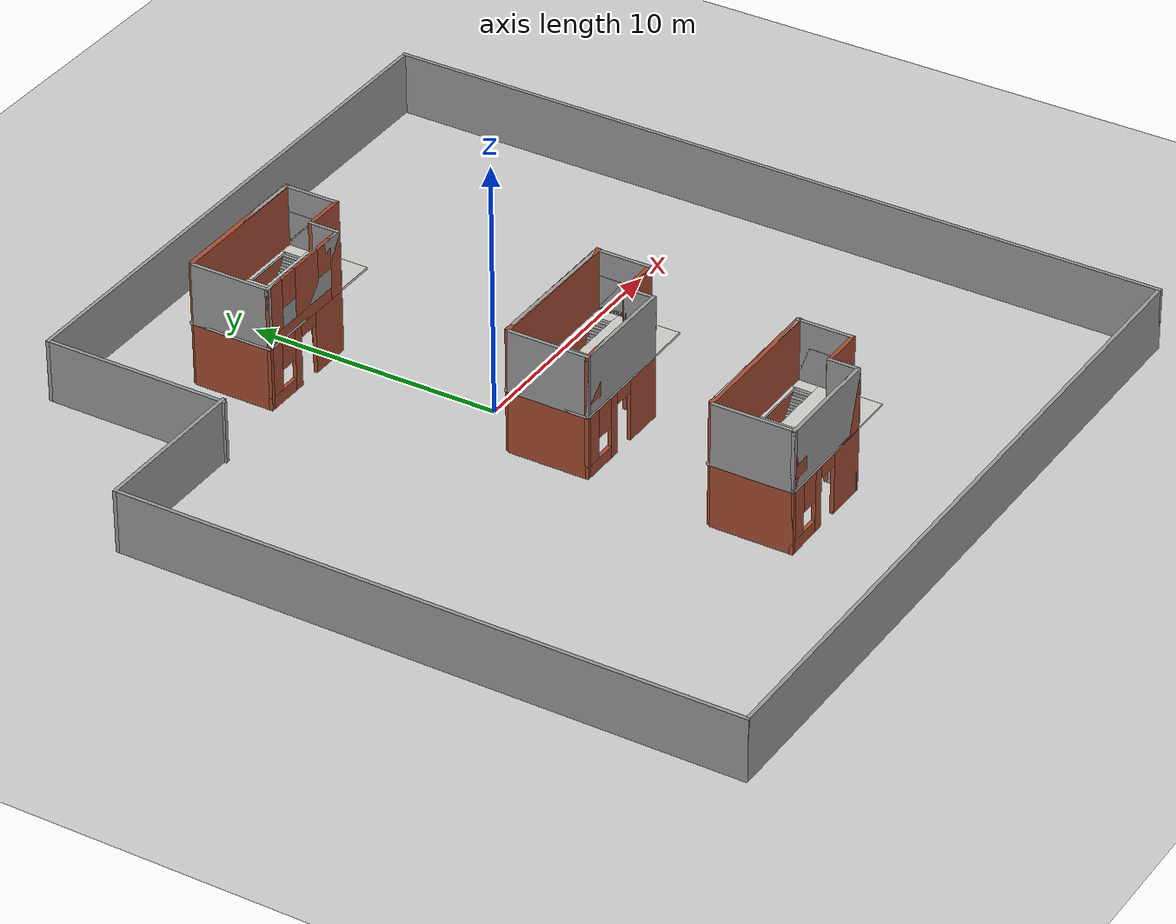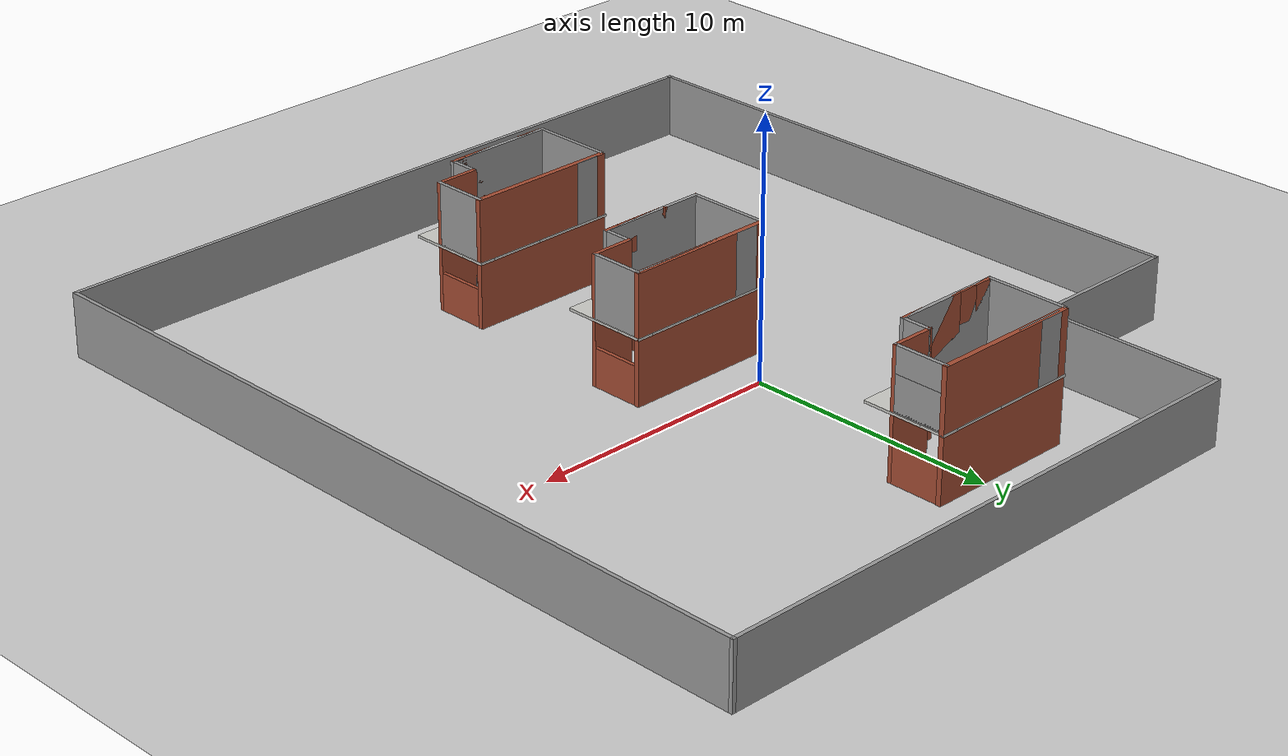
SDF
<sdf version="1.7">
 <world name="default">
  <light name="sun" type="directional">
   <pose>0 0 10 0 -0 0</pose>
   <diffuse>0.8 0.8 0.8 1</diffuse>
   <specular>0.2 0.2 0.2 1</specular>
   <attenuation>
    <range>1000</range>
    <constant>0.9</constant>
    <linear>0.01</linear>
    <quadratic>0.001</quadratic>
   </attenuation>
   <direction>-0.5 0.1 -0.9</direction>
   <spot><inner_angle>0</inner_angle><outer_angle>0</outer_angle><falloff>0</falloff></spot>
  </light>
  <model name="ground_plane">
   <static>1</static>
   <link name="link">
    <collision name="collision">
     <geometry><plane><normal>0 0 1</normal><size>100 100</size></plane></geometry>
     <surface><friction><ode><mu>100</mu><mu2>50</mu2></ode></friction></surface>
    </collision>
    <visual name="visual">
     <cast_shadows>0</cast_shadows>
     <geometry><plane><normal>0 0 1</normal><size>100 100</size></plane></geometry>
     <material>
      <script><uri>file://media/materials/scripts/gazebo.material</uri><name>Gazebo/Grey</name></script>
     </material>
    </visual>
   </link>
  </model>
  <gravity>0 0 -9.8</gravity>
  <magnetic_field>6e-06 2.3e-05 -4.2e-05</magnetic_field>
  <atmosphere type="adiabatic"/>
  <physics type="ode">
   <max_step_size>0.001</max_step_size>
   <real_time_factor>1</real_time_factor>
   <real_time_update_rate>1000</real_time_update_rate>
  </physics>
  <scene><ambient>0.4 0.4 0.4 1</ambient><background>0.7 0.7 0.7 1</background><shadows>1</shadows></scene>
  <spherical_coordinates>
   <surface_model>EARTH_WGS84</surface_model>
   <latitude_deg>0</latitude_deg>
   <longitude_deg>0</longitude_deg>
   <elevation>0</elevation>
   <heading_deg>0</heading_deg>
  </spherical_coordinates>
  <model name="my_building">
   <pose>1.1975 -2.4925 0 0 -0 0</pose>
   <link name="Floor_0">
    <pose>-0 -0.802297 2.5 0 -0 0</pose>
    <visual name="Floor_0_Visual_0">
     <pose>-1.405 0 0.05 0 -0 0</pose>
     <geometry><box><size>3.315 3.38041 0.1</size></box></geometry>
     <material>
      <script><uri>file://media/materials/scripts/gazebo.material</uri><name>Gazebo/CeilingTiled</name></script>
      <ambient>1 1 1 1</ambient>
     </material>
     <meta><layer>1</layer></meta>
    </visual>
    <collision name="Floor_0_Collision_0">
     <geometry><box><size>3.315 3.38041 0.1</size></box></geometry>
     <pose>-1.405 0 0.05 0 -0 0</pose>
    </collision>
    <visual name="Floor_0_Visual_1">
     <pose>1.6575 -0.492703 0.05 0 -0 0</pose>
     <geometry><box><size>2.81 2.395 0.1</size></box></geometry>
     <material>
      <script><uri>file://media/materials/scripts/gazebo.material</uri><name>Gazebo/CeilingTiled</name></script>
      <ambient>1 1 1 1</ambient>
     </material>
     <meta><layer>1</layer></meta>
    </visual>
    <collision name="Floor_0_Collision_1">
     <geometry><box><size>2.81 2.395 0.1</size></box></geometry>
     <pose>1.6575 -0.492703 0.05 0 -0 0</pose>
    </collision>
    <visual name="Floor_0_Visual_2">
     <pose>2.7375 1.1975 0.05 0 -0 0</pose>
     <geometry><box><size>0.65 0.985407 0.1</size></box></geometry>
     <material>
      <script><uri>file://media/materials/scripts/gazebo.material</uri><name>Gazebo/CeilingTiled</name></script>
      <ambient>1 1 1 1</ambient>
     </material>
     <meta><layer>1</layer></meta>
    </visual>
    <collision name="Floor_0_Collision_2">
     <geometry><box><size>0.65 0.985407 0.1</size></box></geometry>
     <pose>2.7375 1.1975 0.05 0 -0 0</pose>
    </collision>
    <visual name="Floor_0_Visual_3">
     <pose>1.3325 1.5275 0.05 0 -0 0</pose>
     <geometry><box><size>2.16 0.325407 0.1</size></box></geometry>
     <material>
      <script><uri>file://media/materials/scripts/gazebo.material</uri><name>Gazebo/CeilingTiled</name></script>
      <ambient>1 1 1 1</ambient>
     </material>
     <meta><layer>1</layer></meta>
    </visual>
    <collision name="Floor_0_Collision_3">
     <geometry><box><size>2.16 0.325407 0.1</size></box></geometry>
     <pose>1.3325 1.5275 0.05 0 -0 0</pose>
    </collision>
   </link>
   <link name="Stairs_0">
    <visual name="Stairs_0_Visual_0">
     <pose>0.3245 0.2325 0.083333 0 -0 1.5708</pose>
     <geometry><box><size>0.66 0.144 0.166667</size></box></geometry>
     <material>
      <script><uri>file://media/materials/scripts/gazebo.material</uri><name>Gazebo/Grey</name></script>
      <ambient>1 1 1 1</ambient>
     </material>
     <meta><layer>0</layer></meta>
    </visual>
    <collision name="Stairs_0_Collision_0">
     <geometry><box><size>0.66 0.144 0.166667</size></box></geometry>
     <pose>0.3245 0.2325 0.083333 0 -0 1.5708</pose>
    </collision>
    <visual name="Stairs_0_Visual_1">
     <pose>0.4685 0.2325 0.25 0 -0 1.5708</pose>
     <geometry><box><size>0.66 0.144 0.166667</size></box></geometry>
     <material>
      <script><uri>file://media/materials/scripts/gazebo.material</uri><name>Gazebo/Grey</name></script>
      <ambient>1 1 1 1</ambient>
     </material>
     <meta><layer>0</layer></meta>
    </visual>
    <collision name="Stairs_0_Collision_1">
     <geometry><box><size>0.66 0.144 0.166667</size></box></geometry>
     <pose>0.4685 0.2325 0.25 0 -0 1.5708</pose>
    </collision>
    <visual name="Stairs_0_Visual_2">
     <pose>0.6125 0.2325 0.416667 0 -0 1.5708</pose>
     <geometry><box><size>0.66 0.144 0.166667</size></box></geometry>
     <material>
      <script><uri>file://media/materials/scripts/gazebo.material</uri><name>Gazebo/Grey</name></script>
      <ambient>1 1 1 1</ambient>
     </material>
     <meta><layer>0</layer></meta>
    </visual>
    <collision name="Stairs_0_Collision_2">
     <geometry><box><size>0.66 0.144 0.166667</size></box></geometry>
     <pose>0.6125 0.2325 0.416667 0 -0 1.5708</pose>
    </collision>
    <visual name="Stairs_0_Visual_3">
     <pose>0.7565 0.2325 0.583333 0 -0 1.5708</pose>
     <geometry><box><size>0.66 0.144 0.166667</size></box></geometry>
     <material>
      <script><uri>file://media/materials/scripts/gazebo.material</uri><name>Gazebo/Grey</name></script>
      <ambient>1 1 1 1</ambient>
     </material>
     <meta><layer>0</layer></meta>
    </visual>
    <collision name="Stairs_0_Collision_3">
     <geometry><box><size>0.66 0.144 0.166667</size></box></geometry>
     <pose>0.7565 0.2325 0.583333 0 -0 1.5708</pose>
    </collision>
    <visual name="Stairs_0_Visual_4">
     <pose>0.9005 0.2325 0.75 0 -0 1.5708</pose>
     <geometry><box><size>0.66 0.144 0.166667</size></box></geometry>
     <material>
      <script><uri>file://media/materials/scripts/gazebo.material</uri><name>Gazebo/Grey</name></script>
      <ambient>1 1 1 1</ambient>
     </material>
     <meta><layer>0</layer></meta>
    </visual>
    <collision name="Stairs_0_Collision_4">
     <geometry><box><size>0.66 0.144 0.166667</size></box></geometry>
     <pose>0.9005 0.2325 0.75 0 -0 1.5708</pose>
    </collision>
    <visual name="Stairs_0_Visual_5">
     <pose>1.0445 0.2325 0.916667 0 -0 1.5708</pose>
     <geometry><box><size>0.66 0.144 0.166667</size></box></geometry>
     <material>
      <script><uri>file://media/materials/scripts/gazebo.material</uri><name>Gazebo/Grey</name></script>
      <ambient>1 1 1 1</ambient>
     </material>
     <meta><layer>0</layer></meta>
    </visual>
    <collision name="Stairs_0_Collision_5">
     <geometry><box><size>0.66 0.144 0.166667</size></box></geometry>
     <pose>1.0445 0.2325 0.916667 0 -0 1.5708</pose>
    </collision>
    <visual name="Stairs_0_Visual_6">
     <pose>1.1885 0.2325 1.08333 0 -0 1.5708</pose>
     <geometry><box><size>0.66 0.144 0.166667</size></box></geometry>
     <material>
      <script><uri>file://media/materials/scripts/gazebo.material</uri><name>Gazebo/Grey</name></script>
      <ambient>1 1 1 1</ambient>
     </material>
     <meta><layer>0</layer></meta>
    </visual>
    <collision name="Stairs_0_Collision_6">
     <geometry><box><size>0.66 0.144 0.166667</size></box></geometry>
     <pose>1.1885 0.2325 1.08333 0 -0 1.5708</pose>
    </collision>
    <visual name="Stairs_0_Visual_7">
     <pose>1.3325 0.2325 1.25 0 -0 1.5708</pose>
     <geometry><box><size>0.66 0.144 0.166667</size></box></geometry>
     <material>
      <script><uri>file://media/materials/scripts/gazebo.material</uri><name>Gazebo/Grey</name></script>
      <ambient>1 1 1 1</ambient>
     </material>
     <meta><layer>0</layer></meta>
    </visual>
    <collision name="Stairs_0_Collision_7">
     <geometry><box><size>0.66 0.144 0.166667</size></box></geometry>
     <pose>1.3325 0.2325 1.25 0 -0 1.5708</pose>
    </collision>
    <visual name="Stairs_0_Visual_8">
     <pose>1.4765 0.2325 1.41667 0 -0 1.5708</pose>
     <geometry><box><size>0.66 0.144 0.166667</size></box></geometry>
     <material>
      <script><uri>file://media/materials/scripts/gazebo.material</uri><name>Gazebo/Grey</name></script>
      <ambient>1 1 1 1</ambient>
     </material>
     <meta><layer>0</layer></meta>
    </visual>
    <collision name="Stairs_0_Collision_8">
     <geometry><box><size>0.66 0.144 0.166667</size></box></geometry>
     <pose>1.4765 0.2325 1.41667 0 -0 1.5708</pose>
    </collision>
    <visual name="Stairs_0_Visual_9">
     <pose>1.6205 0.2325 1.58333 0 -0 1.5708</pose>
     <geometry><box><size>0.66 0.144 0.166667</size></box></geometry>
     <material>
      <script><uri>file://media/materials/scripts/gazebo.material</uri><name>Gazebo/Grey</name></script>
      <ambient>1 1 1 1</ambient>
     </material>
     <meta><layer>0</layer></meta>
    </visual>
    <collision name="Stairs_0_Collision_9">
     <geometry><box><size>0.66 0.144 0.166667</size></box></geometry>
     <pose>1.6205 0.2325 1.58333 0 -0 1.5708</pose>
    </collision>
    <visual name="Stairs_0_Visual_10">
     <pose>1.7645 0.2325 1.75 0 -0 1.5708</pose>
     <geometry><box><size>0.66 0.144 0.166667</size></box></geometry>
     <material>
      <script><uri>file://media/materials/scripts/gazebo.material</uri><name>Gazebo/Grey</name></script>
      <ambient>1 1 1 1</ambient>
     </material>
     <meta><layer>0</layer></meta>
    </visual>
    <collision name="Stairs_0_Collision_10">
     <geometry><box><size>0.66 0.144 0.166667</size></box></geometry>
     <pose>1.7645 0.2325 1.75 0 -0 1.5708</pose>
    </collision>
    <visual name="Stairs_0_Visual_11">
     <pose>1.9085 0.2325 1.91667 0 -0 1.5708</pose>
     <geometry><box><size>0.66 0.144 0.166667</size></box></geometry>
     <material>
      <script><uri>file://media/materials/scripts/gazebo.material</uri><name>Gazebo/Grey</name></script>
      <ambient>1 1 1 1</ambient>
     </material>
     <meta><layer>0</layer></meta>
    </visual>
    <collision name="Stairs_0_Collision_11">
     <geometry><box><size>0.66 0.144 0.166667</size></box></geometry>
     <pose>1.9085 0.2325 1.91667 0 -0 1.5708</pose>
    </collision>
    <visual name="Stairs_0_Visual_12">
     <pose>2.0525 0.2325 2.08333 0 -0 1.5708</pose>
     <geometry><box><size>0.66 0.144 0.166667</size></box></geometry>
     <material>
      <script><uri>file://media/materials/scripts/gazebo.material</uri><name>Gazebo/Grey</name></script>
      <ambient>1 1 1 1</ambient>
     </material>
     <meta><layer>0</layer></meta>
    </visual>
    <collision name="Stairs_0_Collision_12">
     <geometry><box><size>0.66 0.144 0.166667</size></box></geometry>
     <pose>2.0525 0.2325 2.08333 0 -0 1.5708</pose>
    </collision>
    <visual name="Stairs_0_Visual_13">
     <pose>2.1965 0.2325 2.25 0 -0 1.5708</pose>
     <geometry><box><size>0.66 0.144 0.166667</size></box></geometry>
     <material>
      <script><uri>file://media/materials/scripts/gazebo.material</uri><name>Gazebo/Grey</name></script>
      <ambient>1 1 1 1</ambient>
     </material>
     <meta><layer>0</layer></meta>
    </visual>
    <collision name="Stairs_0_Collision_13">
     <geometry><box><size>0.66 0.144 0.166667</size></box></geometry>
     <pose>2.1965 0.2325 2.25 0 -0 1.5708</pose>
    </collision>
    <visual name="Stairs_0_Visual_14">
     <pose>2.3405 0.2325 2.41667 0 -0 1.5708</pose>
     <geometry><box><size>0.66 0.144 0.166667</size></box></geometry>
     <material>
      <script><uri>file://media/materials/scripts/gazebo.material</uri><name>Gazebo/Grey</name></script>
      <ambient>1 1 1 1</ambient>
     </material>
     <meta><layer>0</layer></meta>
    </visual>
    <collision name="Stairs_0_Collision_14">
     <geometry><box><size>0.66 0.144 0.166667</size></box></geometry>
     <pose>2.3405 0.2325 2.41667 0 -0 1.5708</pose>
    </collision>
   </link>
   <link name="Wall_0">
    <collision name="Wall_0_Collision">
     <geometry><box><size>6.05 0.2 2.5</size></box></geometry>
     <pose>0 0 1.25 0 -0 0</pose>
    </collision>
    <visual name="Wall_0_Visual">
     <pose>0 0 1.25 0 -0 0</pose>
     <geometry><box><size>6.05 0.2 2.5</size></box></geometry>
     <material>
      <script><uri>file://media/materials/scripts/gazebo.material</uri><name>Gazebo/Bricks</name></script>
      <ambient>1 1 1 1</ambient>
     </material>
     <meta><layer>0</layer></meta>
    </visual>
    <pose>0.0375 0.7825 0 0 -0 0</pose>
   </link>
   <link name="Wall_1">
    <collision name="Wall_1_Collision">
     <geometry><box><size>2.25 0.15 1.5</size></box></geometry>
     <pose>0 0 0.75 0 -0 0</pose>
    </collision>
    <visual name="Wall_1_Visual">
     <pose>0 0 0.75 0 -0 0</pose>
     <geometry><box><size>2.25 0.15 1.5</size></box></geometry>
     <material>
      <script><uri>file://media/materials/scripts/gazebo.material</uri><name>Gazebo/Bricks</name></script>
      <ambient>1 1 1 1</ambient>
     </material>
     <meta><layer>0</layer></meta>
    </visual>
    <pose>2.9625 -0.2675 0 0 -0 -1.5708</pose>
   </link>
   <link name="Wall_10">
    <collision name="Wall_10_Collision">
     <geometry><box><size>1.25 0.15 2.5</size></box></geometry>
     <pose>0 0 1.25 0 -0 0</pose>
    </collision>
    <visual name="Wall_10_Visual">
     <pose>0 0 1.25 0 -0 0</pose>
     <geometry><box><size>1.25 0.15 2.5</size></box></geometry>
     <material>
      <script><uri>file://media/materials/scripts/gazebo.material</uri><name>Gazebo/Grey</name></script>
      <ambient>1 1 1 1</ambient>
     </material>
     <meta><layer>1</layer></meta>
    </visual>
    <pose>1.3625 -1.8675 2.5 0 -0 -1.5708</pose>
   </link>
   <link name="Wall_11">
    <collision name="Wall_11_Collision">
     <geometry><box><size>4.5 0.15 2.5</size></box></geometry>
     <pose>0 0 1.25 0 -0 0</pose>
    </collision>
    <visual name="Wall_11_Visual">
     <pose>0 0 1.25 0 -0 0</pose>
     <geometry><box><size>4.5 0.15 2.5</size></box></geometry>
     <material>
      <script><uri>file://media/materials/scripts/gazebo.material</uri><name>Gazebo/Grey</name></script>
      <ambient>1 1 1 1</ambient>
     </material>
     <meta><layer>1</layer></meta>
    </visual>
    <pose>-0.8125 -2.4175 2.5 0 -0 3.14159</pose>
   </link>
   <link name="Wall_12">
    <collision name="Wall_12_Collision">
     <geometry><box><size>3.25 0.15 2.5</size></box></geometry>
     <pose>0 0 1.25 0 -0 0</pose>
    </collision>
    <visual name="Wall_12_Visual">
     <pose>0 0 1.25 0 -0 0</pose>
     <geometry><box><size>3.25 0.15 2.5</size></box></geometry>
     <material>
      <script><uri>file://media/materials/scripts/gazebo.material</uri><name>Gazebo/Grey</name></script>
      <ambient>1 1 1 1</ambient>
     </material>
     <meta><layer>1</layer></meta>
    </visual>
    <pose>-2.9875 -0.8675 2.5 0 -0 1.5708</pose>
   </link>
   <link name="Wall_14">
    <collision name="Wall_14_Collision">
     <geometry><box><size>5.67008 0.15 2.5</size></box></geometry>
     <pose>0 0 1.25 0 -0 0</pose>
    </collision>
    <visual name="Wall_14_Visual">
     <pose>0 0 1.25 0 -0 0</pose>
     <geometry><box><size>5.67008 0.15 2.5</size></box></geometry>
     <material>
      <script><uri>file://media/materials/scripts/gazebo.material</uri><name>Gazebo/Grey</name></script>
      <ambient>1 1 1 1</ambient>
     </material>
     <meta><layer>1</layer></meta>
    </visual>
    <pose>0.2025 0.7975 2.5 0 -0 -0.005435</pose>
   </link>
   <link name="Wall_15">
    <collision name="Wall_15_Collision">
     <geometry><box><size>2.25 0.15 2.5</size></box></geometry>
     <pose>0 0 1.25 0 -0 0</pose>
    </collision>
    <visual name="Wall_15_Visual">
     <pose>0 0 1.25 0 -0 0</pose>
     <geometry><box><size>2.25 0.15 2.5</size></box></geometry>
     <material>
      <script><uri>file://media/materials/scripts/gazebo.material</uri><name>Gazebo/Grey</name></script>
      <ambient>1 1 1 1</ambient>
     </material>
     <meta><layer>1</layer></meta>
    </visual>
    <pose>2.9625 -0.2675 2.5 0 -0 -1.5708</pose>
   </link>
   <link name="Wall_16">
    <collision name="Wall_16_Collision">
     <geometry><box><size>1.75 0.15 2.5</size></box></geometry>
     <pose>0 0 1.25 0 -0 0</pose>
    </collision>
    <visual name="Wall_16_Visual">
     <pose>0 0 1.25 0 -0 0</pose>
     <geometry><box><size>1.75 0.15 2.5</size></box></geometry>
     <material>
      <script><uri>file://media/materials/scripts/gazebo.material</uri><name>Gazebo/Bricks</name></script>
      <ambient>1 1 1 1</ambient>
     </material>
     <meta><layer>1</layer></meta>
    </visual>
    <pose>2.1625 -1.3175 2.5 0 -0 3.14159</pose>
   </link>
   <link name="Wall_17">
    <collision name="Wall_17_Collision">
     <geometry><box><size>1.25 0.15 2.5</size></box></geometry>
     <pose>0 0 1.25 0 -0 0</pose>
    </collision>
    <visual name="Wall_17_Visual">
     <pose>0 0 1.25 0 -0 0</pose>
     <geometry><box><size>1.25 0.15 2.5</size></box></geometry>
     <material>
      <script><uri>file://media/materials/scripts/gazebo.material</uri><name>Gazebo/Grey</name></script>
      <ambient>1 1 1 1</ambient>
     </material>
     <meta><layer>1</layer></meta>
    </visual>
    <pose>1.3625 -1.8675 2.5 0 -0 -1.5708</pose>
   </link>
   <link name="Wall_18">
    <pose>-0.8125 -2.4175 2.5 0 -0 3.14159</pose>
    <visual name="Wall_18_Visual_0">
     <pose>-1.9275 0 1.25 0 -0 0</pose>
     <geometry><box><size>0.645 0.15 2.5</size></box></geometry>
     <material>
      <script><uri>file://media/materials/scripts/gazebo.material</uri><name>Gazebo/Bricks</name></script>
      <ambient>1 1 1 1</ambient>
     </material>
     <meta><layer>1</layer></meta>
    </visual>
    <collision name="Wall_18_Collision_0">
     <geometry><box><size>0.645 0.15 2.5</size></box></geometry>
     <pose>-1.9275 0 1.25 0 -0 0</pose>
    </collision>
    <visual name="Wall_18_Visual_1">
     <pose>0.3225 0 0.25 0 -0 0</pose>
     <geometry><box><size>3.855 0.15 0.5</size></box></geometry>
     <material>
      <script><uri>file://media/materials/scripts/gazebo.material</uri><name>Gazebo/Bricks</name></script>
      <ambient>1 1 1 1</ambient>
     </material>
     <meta><layer>1</layer></meta>
    </visual>
    <collision name="Wall_18_Collision_1">
     <geometry><box><size>3.855 0.15 0.5</size></box></geometry>
     <pose>0.3225 0 0.25 0 -0 0</pose>
    </collision>
    <visual name="Wall_18_Visual_2">
     <pose>-0.095 0 1.5 0 -0 0</pose>
     <geometry><box><size>1.42 0.15 2</size></box></geometry>
     <material>
      <script><uri>file://media/materials/scripts/gazebo.material</uri><name>Gazebo/Bricks</name></script>
      <ambient>1 1 1 1</ambient>
     </material>
     <meta><layer>1</layer></meta>
    </visual>
    <collision name="Wall_18_Collision_2">
     <geometry><box><size>1.42 0.15 2</size></box></geometry>
     <pose>-0.095 0 1.5 0 -0 0</pose>
    </collision>
    <visual name="Wall_18_Visual_3">
     <pose>1.8325 0 1.5 0 -0 0</pose>
     <geometry><box><size>0.835 0.15 2</size></box></geometry>
     <material>
      <script><uri>file://media/materials/scripts/gazebo.material</uri><name>Gazebo/Bricks</name></script>
      <ambient>1 1 1 1</ambient>
     </material>
     <meta><layer>1</layer></meta>
    </visual>
    <collision name="Wall_18_Collision_3">
     <geometry><box><size>0.835 0.15 2</size></box></geometry>
     <pose>1.8325 0 1.5 0 -0 0</pose>
    </collision>
    <visual name="Wall_18_Visual_4">
     <pose>-1.205 0 1.9 0 -0 0</pose>
     <geometry><box><size>0.8 0.15 1.2</size></box></geometry>
     <material>
      <script><uri>file://media/materials/scripts/gazebo.material</uri><name>Gazebo/Bricks</name></script>
      <ambient>1 1 1 1</ambient>
     </material>
     <meta><layer>1</layer></meta>
    </visual>
    <collision name="Wall_18_Collision_4">
     <geometry><box><size>0.8 0.15 1.2</size></box></geometry>
     <pose>-1.205 0 1.9 0 -0 0</pose>
    </collision>
    <visual name="Wall_18_Visual_5">
     <pose>1.015 0 1.9 0 -0 0</pose>
     <geometry><box><size>0.8 0.15 1.2</size></box></geometry>
     <material>
      <script><uri>file://media/materials/scripts/gazebo.material</uri><name>Gazebo/Bricks</name></script>
      <ambient>1 1 1 1</ambient>
     </material>
     <meta><layer>1</layer></meta>
    </visual>
    <collision name="Wall_18_Collision_5">
     <geometry><box><size>0.8 0.15 1.2</size></box></geometry>
     <pose>1.015 0 1.9 0 -0 0</pose>
    </collision>
   </link>
   <link name="Wall_19">
    <collision name="Wall_19_Collision">
     <geometry><box><size>3.25 0.15 2.5</size></box></geometry>
     <pose>0 0 1.25 0 -0 0</pose>
    </collision>
    <visual name="Wall_19_Visual">
     <pose>0 0 1.25 0 -0 0</pose>
     <geometry><box><size>3.25 0.15 2.5</size></box></geometry>
     <material>
      <script><uri>file://media/materials/scripts/gazebo.material</uri><name>Gazebo/Bricks</name></script>
      <ambient>1 1 1 1</ambient>
     </material>
     <meta><layer>1</layer></meta>
    </visual>
    <pose>-2.9875 -0.8675 2.5 0 -0 1.5708</pose>
   </link>
   <link name="Wall_2">
    <collision name="Wall_2_Collision">
     <geometry><box><size>1.75 0.15 2.5</size></box></geometry>
     <pose>0 0 1.25 0 -0 0</pose>
    </collision>
    <visual name="Wall_2_Visual">
     <pose>0 0 1.25 0 -0 0</pose>
     <geometry><box><size>1.75 0.15 2.5</size></box></geometry>
     <material>
      <script><uri>file://media/materials/scripts/gazebo.material</uri><name>Gazebo/Bricks</name></script>
      <ambient>1 1 1 1</ambient>
     </material>
     <meta><layer>0</layer></meta>
    </visual>
    <pose>2.1625 -1.3175 0 0 -0 3.14159</pose>
   </link>
   <link name="Wall_3">
    <collision name="Wall_3_Collision">
     <geometry><box><size>1.25 0.15 2.5</size></box></geometry>
     <pose>0 0 1.25 0 -0 0</pose>
    </collision>
    <visual name="Wall_3_Visual">
     <pose>0 0 1.25 0 -0 0</pose>
     <geometry><box><size>1.25 0.15 2.5</size></box></geometry>
     <material>
      <script><uri>file://media/materials/scripts/gazebo.material</uri><name>Gazebo/Grey</name></script>
      <ambient>1 1 1 1</ambient>
     </material>
     <meta><layer>0</layer></meta>
    </visual>
    <pose>1.3625 -1.8675 0 0 -0 -1.5708</pose>
   </link>
   <link name="Wall_4">
    <pose>-0.8125 -2.4175 0 0 -0 3.14159</pose>
    <visual name="Wall_4_Visual_0">
     <pose>-1.4025 0 1.25 0 -0 0</pose>
     <geometry><box><size>1.695 0.15 2.5</size></box></geometry>
     <material>
      <script><uri>file://media/materials/scripts/gazebo.material</uri><name>Gazebo/Bricks</name></script>
      <ambient>1 1 1 1</ambient>
     </material>
     <meta><layer>0</layer></meta>
    </visual>
    <collision name="Wall_4_Collision_0">
     <geometry><box><size>1.695 0.15 2.5</size></box></geometry>
     <pose>-1.4025 0 1.25 0 -0 0</pose>
    </collision>
    <visual name="Wall_4_Visual_1">
     <pose>0.54 0 1.25 0 -0 0</pose>
     <geometry><box><size>0.39 0.15 2.5</size></box></geometry>
     <material>
      <script><uri>file://media/materials/scripts/gazebo.material</uri><name>Gazebo/Bricks</name></script>
      <ambient>1 1 1 1</ambient>
     </material>
     <meta><layer>0</layer></meta>
    </visual>
    <collision name="Wall_4_Collision_1">
     <geometry><box><size>0.39 0.15 2.5</size></box></geometry>
     <pose>0.54 0 1.25 0 -0 0</pose>
    </collision>
    <visual name="Wall_4_Visual_2">
     <pose>1.4925 0 0.25 0 -0 0</pose>
     <geometry><box><size>1.515 0.15 0.5</size></box></geometry>
     <material>
      <script><uri>file://media/materials/scripts/gazebo.material</uri><name>Gazebo/Bricks</name></script>
      <ambient>1 1 1 1</ambient>
     </material>
     <meta><layer>0</layer></meta>
    </visual>
    <collision name="Wall_4_Collision_2">
     <geometry><box><size>1.515 0.15 0.5</size></box></geometry>
     <pose>1.4925 0 0.25 0 -0 0</pose>
    </collision>
    <visual name="Wall_4_Visual_3">
     <pose>1.8925 0 1.5 0 -0 0</pose>
     <geometry><box><size>0.715 0.15 2</size></box></geometry>
     <material>
      <script><uri>file://media/materials/scripts/gazebo.material</uri><name>Gazebo/Bricks</name></script>
      <ambient>1 1 1 1</ambient>
     </material>
     <meta><layer>0</layer></meta>
    </visual>
    <collision name="Wall_4_Collision_3">
     <geometry><box><size>0.715 0.15 2</size></box></geometry>
     <pose>1.8925 0 1.5 0 -0 0</pose>
    </collision>
    <visual name="Wall_4_Visual_4">
     <pose>1.135 0 1.9 0 -0 0</pose>
     <geometry><box><size>0.8 0.15 1.2</size></box></geometry>
     <material>
      <script><uri>file://media/materials/scripts/gazebo.material</uri><name>Gazebo/Bricks</name></script>
      <ambient>1 1 1 1</ambient>
     </material>
     <meta><layer>0</layer></meta>
    </visual>
    <collision name="Wall_4_Collision_4">
     <geometry><box><size>0.8 0.15 1.2</size></box></geometry>
     <pose>1.135 0 1.9 0 -0 0</pose>
    </collision>
    <visual name="Wall_4_Visual_5">
     <pose>-0.105 0 2.25 0 -0 0</pose>
     <geometry><box><size>0.9 0.15 0.5</size></box></geometry>
     <material>
      <script><uri>file://media/materials/scripts/gazebo.material</uri><name>Gazebo/Bricks</name></script>
      <ambient>1 1 1 1</ambient>
     </material>
     <meta><layer>0</layer></meta>
    </visual>
    <collision name="Wall_4_Collision_5">
     <geometry><box><size>0.9 0.15 0.5</size></box></geometry>
     <pose>-0.105 0 2.25 0 -0 0</pose>
    </collision>
   </link>
   <link name="Wall_5">
    <collision name="Wall_5_Collision">
     <geometry><box><size>3.25 0.15 2.5</size></box></geometry>
     <pose>0 0 1.25 0 -0 0</pose>
    </collision>
    <visual name="Wall_5_Visual">
     <pose>0 0 1.25 0 -0 0</pose>
     <geometry><box><size>3.25 0.15 2.5</size></box></geometry>
     <material>
      <script><uri>file://media/materials/scripts/gazebo.material</uri><name>Gazebo/Bricks</name></script>
      <ambient>1 1 1 1</ambient>
     </material>
     <meta><layer>0</layer></meta>
    </visual>
    <pose>-2.9875 -0.8675 0 0 -0 1.5708</pose>
   </link>
   <link name="Wall_7">
    <collision name="Wall_7_Collision">
     <geometry><box><size>6.05 0.2 2.5</size></box></geometry>
     <pose>0 0 1.25 0 -0 0</pose>
    </collision>
    <visual name="Wall_7_Visual">
     <pose>0 0 1.25 0 -0 0</pose>
     <geometry><box><size>6.05 0.2 2.5</size></box></geometry>
     <material>
      <script><uri>file://media/materials/scripts/gazebo.material</uri><name>Gazebo/Bricks</name></script>
      <ambient>1 1 1 1</ambient>
     </material>
     <meta><layer>1</layer></meta>
    </visual>
    <pose>0.0375 0.7825 2.5 0 -0 0</pose>
   </link>
   <link name="Wall_8">
    <collision name="Wall_8_Collision">
     <geometry><box><size>2.25 0.15 1.5</size></box></geometry>
     <pose>0 0 0.75 0 -0 0</pose>
    </collision>
    <visual name="Wall_8_Visual">
     <pose>0 0 0.75 0 -0 0</pose>
     <geometry><box><size>2.25 0.15 1.5</size></box></geometry>
     <material>
      <script><uri>file://media/materials/scripts/gazebo.material</uri><name>Gazebo/Grey</name></script>
      <ambient>1 1 1 1</ambient>
     </material>
     <meta><layer>1</layer></meta>
    </visual>
    <pose>2.9625 -0.2675 2.5 0 -0 -1.5708</pose>
   </link>
   <link name="Wall_9">
    <collision name="Wall_9_Collision">
     <geometry><box><size>1.75 0.15 2.5</size></box></geometry>
     <pose>0 0 1.25 0 -0 0</pose>
    </collision>
    <visual name="Wall_9_Visual">
     <pose>0 0 1.25 0 -0 0</pose>
     <geometry><box><size>1.75 0.15 2.5</size></box></geometry>
     <material>
      <script><uri>file://media/materials/scripts/gazebo.material</uri><name>Gazebo/Grey</name></script>
      <ambient>1 1 1 1</ambient>
     </material>
     <meta><layer>1</layer></meta>
    </visual>
    <pose>2.1625 -1.3175 2.5 0 -0 3.14159</pose>
   </link>
   <static>1</static>
  </model>
  <model name="my_building_0">
   <pose>0.946275 -10.6648 0 0 -0 0</pose>
   <link name="Floor_0">
    <pose>-0 -0.802297 2.5 0 -0 0</pose>
    <visual name="Floor_0_Visual_0">
     <pose>-1.405 0 0.05 0 -0 0</pose>
     <geometry><box><size>3.315 3.38041 0.1</size></box></geometry>
     <material>
      <script><uri>file://media/materials/scripts/gazebo.material</uri><name>Gazebo/CeilingTiled</name></script>
      <ambient>1 1 1 1</ambient>
     </material>
     <meta><layer>1</layer></meta>
    </visual>
    <collision name="Floor_0_Collision_0">
     <geometry><box><size>3.315 3.38041 0.1</size></box></geometry>
     <pose>-1.405 0 0.05 0 -0 0</pose>
    </collision>
    <visual name="Floor_0_Visual_1">
     <pose>1.6575 -0.492703 0.05 0 -0 0</pose>
     <geometry><box><size>2.81 2.395 0.1</size></box></geometry>
     <material>
      <script><uri>file://media/materials/scripts/gazebo.material</uri><name>Gazebo/CeilingTiled</name></script>
      <ambient>1 1 1 1</ambient>
     </material>
     <meta><layer>1</layer></meta>
    </visual>
    <collision name="Floor_0_Collision_1">
     <geometry><box><size>2.81 2.395 0.1</size></box></geometry>
     <pose>1.6575 -0.492703 0.05 0 -0 0</pose>
    </collision>
    <visual name="Floor_0_Visual_2">
     <pose>2.7375 1.1975 0.05 0 -0 0</pose>
     <geometry><box><size>0.65 0.985407 0.1</size></box></geometry>
     <material>
      <script><uri>file://media/materials/scripts/gazebo.material</uri><name>Gazebo/CeilingTiled</name></script>
      <ambient>1 1 1 1</ambient>
     </material>
     <meta><layer>1</layer></meta>
    </visual>
    <collision name="Floor_0_Collision_2">
     <geometry><box><size>0.65 0.985407 0.1</size></box></geometry>
     <pose>2.7375 1.1975 0.05 0 -0 0</pose>
    </collision>
    <visual name="Floor_0_Visual_3">
     <pose>1.3325 1.5275 0.05 0 -0 0</pose>
     <geometry><box><size>2.16 0.325407 0.1</size></box></geometry>
     <material>
      <script><uri>file://media/materials/scripts/gazebo.material</uri><name>Gazebo/CeilingTiled</name></script>
      <ambient>1 1 1 1</ambient>
     </material>
     <meta><layer>1</layer></meta>
    </visual>
    <collision name="Floor_0_Collision_3">
     <geometry><box><size>2.16 0.325407 0.1</size></box></geometry>
     <pose>1.3325 1.5275 0.05 0 -0 0</pose>
    </collision>
   </link>
   <link name="Stairs_0">
    <visual name="Stairs_0_Visual_0">
     <pose>0.3245 0.2325 0.083333 0 -0 1.5708</pose>
     <geometry><box><size>0.66 0.144 0.166667</size></box></geometry>
     <material>
      <script><uri>file://media/materials/scripts/gazebo.material</uri><name>Gazebo/Grey</name></script>
      <ambient>1 1 1 1</ambient>
     </material>
     <meta><layer>0</layer></meta>
    </visual>
    <collision name="Stairs_0_Collision_0">
     <geometry><box><size>0.66 0.144 0.166667</size></box></geometry>
     <pose>0.3245 0.2325 0.083333 0 -0 1.5708</pose>
    </collision>
    <visual name="Stairs_0_Visual_1">
     <pose>0.4685 0.2325 0.25 0 -0 1.5708</pose>
     <geometry><box><size>0.66 0.144 0.166667</size></box></geometry>
     <material>
      <script><uri>file://media/materials/scripts/gazebo.material</uri><name>Gazebo/Grey</name></script>
      <ambient>1 1 1 1</ambient>
     </material>
     <meta><layer>0</layer></meta>
    </visual>
    <collision name="Stairs_0_Collision_1">
     <geometry><box><size>0.66 0.144 0.166667</size></box></geometry>
     <pose>0.4685 0.2325 0.25 0 -0 1.5708</pose>
    </collision>
    <visual name="Stairs_0_Visual_2">
     <pose>0.6125 0.2325 0.416667 0 -0 1.5708</pose>
     <geometry><box><size>0.66 0.144 0.166667</size></box></geometry>
     <material>
      <script><uri>file://media/materials/scripts/gazebo.material</uri><name>Gazebo/Grey</name></script>
      <ambient>1 1 1 1</ambient>
     </material>
     <meta><layer>0</layer></meta>
    </visual>
    <collision name="Stairs_0_Collision_2">
     <geometry><box><size>0.66 0.144 0.166667</size></box></geometry>
     <pose>0.6125 0.2325 0.416667 0 -0 1.5708</pose>
    </collision>
    <visual name="Stairs_0_Visual_3">
     <pose>0.7565 0.2325 0.583333 0 -0 1.5708</pose>
     <geometry><box><size>0.66 0.144 0.166667</size></box></geometry>
     <material>
      <script><uri>file://media/materials/scripts/gazebo.material</uri><name>Gazebo/Grey</name></script>
      <ambient>1 1 1 1</ambient>
     </material>
     <meta><layer>0</layer></meta>
    </visual>
    <collision name="Stairs_0_Collision_3">
     <geometry><box><size>0.66 0.144 0.166667</size></box></geometry>
     <pose>0.7565 0.2325 0.583333 0 -0 1.5708</pose>
    </collision>
    <visual name="Stairs_0_Visual_4">
     <pose>0.9005 0.2325 0.75 0 -0 1.5708</pose>
     <geometry><box><size>0.66 0.144 0.166667</size></box></geometry>
     <material>
      <script><uri>file://media/materials/scripts/gazebo.material</uri><name>Gazebo/Grey</name></script>
      <ambient>1 1 1 1</ambient>
     </material>
     <meta><layer>0</layer></meta>
    </visual>
    <collision name="Stairs_0_Collision_4">
     <geometry><box><size>0.66 0.144 0.166667</size></box></geometry>
     <pose>0.9005 0.2325 0.75 0 -0 1.5708</pose>
    </collision>
    <visual name="Stairs_0_Visual_5">
     <pose>1.0445 0.2325 0.916667 0 -0 1.5708</pose>
     <geometry><box><size>0.66 0.144 0.166667</size></box></geometry>
     <material>
      <script><uri>file://media/materials/scripts/gazebo.material</uri><name>Gazebo/Grey</name></script>
      <ambient>1 1 1 1</ambient>
     </material>
     <meta><layer>0</layer></meta>
    </visual>
    <collision name="Stairs_0_Collision_5">
     <geometry><box><size>0.66 0.144 0.166667</size></box></geometry>
     <pose>1.0445 0.2325 0.916667 0 -0 1.5708</pose>
    </collision>
    <visual name="Stairs_0_Visual_6">
     <pose>1.1885 0.2325 1.08333 0 -0 1.5708</pose>
     <geometry><box><size>0.66 0.144 0.166667</size></box></geometry>
     <material>
      <script><uri>file://media/materials/scripts/gazebo.material</uri><name>Gazebo/Grey</name></script>
      <ambient>1 1 1 1</ambient>
     </material>
     <meta><layer>0</layer></meta>
    </visual>
    <collision name="Stairs_0_Collision_6">
     <geometry><box><size>0.66 0.144 0.166667</size></box></geometry>
     <pose>1.1885 0.2325 1.08333 0 -0 1.5708</pose>
    </collision>
    <visual name="Stairs_0_Visual_7">
     <pose>1.3325 0.2325 1.25 0 -0 1.5708</pose>
     <geometry><box><size>0.66 0.144 0.166667</size></box></geometry>
     <material>
      <script><uri>file://media/materials/scripts/gazebo.material</uri><name>Gazebo/Grey</name></script>
      <ambient>1 1 1 1</ambient>
     </material>
     <meta><layer>0</layer></meta>
    </visual>
    <collision name="Stairs_0_Collision_7">
     <geometry><box><size>0.66 0.144 0.166667</size></box></geometry>
     <pose>1.3325 0.2325 1.25 0 -0 1.5708</pose>
    </collision>
    <visual name="Stairs_0_Visual_8">
     <pose>1.4765 0.2325 1.41667 0 -0 1.5708</pose>
     <geometry><box><size>0.66 0.144 0.166667</size></box></geometry>
     <material>
      <script><uri>file://media/materials/scripts/gazebo.material</uri><name>Gazebo/Grey</name></script>
      <ambient>1 1 1 1</ambient>
     </material>
     <meta><layer>0</layer></meta>
    </visual>
    <collision name="Stairs_0_Collision_8">
     <geometry><box><size>0.66 0.144 0.166667</size></box></geometry>
     <pose>1.4765 0.2325 1.41667 0 -0 1.5708</pose>
    </collision>
    <visual name="Stairs_0_Visual_9">
     <pose>1.6205 0.2325 1.58333 0 -0 1.5708</pose>
     <geometry><box><size>0.66 0.144 0.166667</size></box></geometry>
     <material>
      <script><uri>file://media/materials/scripts/gazebo.material</uri><name>Gazebo/Grey</name></script>
      <ambient>1 1 1 1</ambient>
     </material>
     <meta><layer>0</layer></meta>
    </visual>
    <collision name="Stairs_0_Collision_9">
     <geometry><box><size>0.66 0.144 0.166667</size></box></geometry>
     <pose>1.6205 0.2325 1.58333 0 -0 1.5708</pose>
    </collision>
    <visual name="Stairs_0_Visual_10">
     <pose>1.7645 0.2325 1.75 0 -0 1.5708</pose>
     <geometry><box><size>0.66 0.144 0.166667</size></box></geometry>
     <material>
      <script><uri>file://media/materials/scripts/gazebo.material</uri><name>Gazebo/Grey</name></script>
      <ambient>1 1 1 1</ambient>
     </material>
     <meta><layer>0</layer></meta>
    </visual>
    <collision name="Stairs_0_Collision_10">
     <geometry><box><size>0.66 0.144 0.166667</size></box></geometry>
     <pose>1.7645 0.2325 1.75 0 -0 1.5708</pose>
    </collision>
    <visual name="Stairs_0_Visual_11">
     <pose>1.9085 0.2325 1.91667 0 -0 1.5708</pose>
     <geometry><box><size>0.66 0.144 0.166667</size></box></geometry>
     <material>
      <script><uri>file://media/materials/scripts/gazebo.material</uri><name>Gazebo/Grey</name></script>
      <ambient>1 1 1 1</ambient>
     </material>
     <meta><layer>0</layer></meta>
    </visual>
    <collision name="Stairs_0_Collision_11">
     <geometry><box><size>0.66 0.144 0.166667</size></box></geometry>
     <pose>1.9085 0.2325 1.91667 0 -0 1.5708</pose>
    </collision>
    <visual name="Stairs_0_Visual_12">
     <pose>2.0525 0.2325 2.08333 0 -0 1.5708</pose>
     <geometry><box><size>0.66 0.144 0.166667</size></box></geometry>
     <material>
      <script><uri>file://media/materials/scripts/gazebo.material</uri><name>Gazebo/Grey</name></script>
      <ambient>1 1 1 1</ambient>
     </material>
     <meta><layer>0</layer></meta>
    </visual>
    <collision name="Stairs_0_Collision_12">
     <geometry><box><size>0.66 0.144 0.166667</size></box></geometry>
     <pose>2.0525 0.2325 2.08333 0 -0 1.5708</pose>
    </collision>
    <visual name="Stairs_0_Visual_13">
     <pose>2.1965 0.2325 2.25 0 -0 1.5708</pose>
     <geometry><box><size>0.66 0.144 0.166667</size></box></geometry>
     <material>
      <script><uri>file://media/materials/scripts/gazebo.material</uri><name>Gazebo/Grey</name></script>
      <ambient>1 1 1 1</ambient>
     </material>
     <meta><layer>0</layer></meta>
    </visual>
    <collision name="Stairs_0_Collision_13">
     <geometry><box><size>0.66 0.144 0.166667</size></box></geometry>
     <pose>2.1965 0.2325 2.25 0 -0 1.5708</pose>
    </collision>
    <visual name="Stairs_0_Visual_14">
     <pose>2.3405 0.2325 2.41667 0 -0 1.5708</pose>
     <geometry><box><size>0.66 0.144 0.166667</size></box></geometry>
     <material>
      <script><uri>file://media/materials/scripts/gazebo.material</uri><name>Gazebo/Grey</name></script>
      <ambient>1 1 1 1</ambient>
     </material>
     <meta><layer>0</layer></meta>
    </visual>
    <collision name="Stairs_0_Collision_14">
     <geometry><box><size>0.66 0.144 0.166667</size></box></geometry>
     <pose>2.3405 0.2325 2.41667 0 -0 1.5708</pose>
    </collision>
   </link>
   <link name="Wall_0">
    <collision name="Wall_0_Collision">
     <geometry><box><size>6.05 0.2 2.5</size></box></geometry>
     <pose>0 0 1.25 0 -0 0</pose>
    </collision>
    <visual name="Wall_0_Visual">
     <pose>0 0 1.25 0 -0 0</pose>
     <geometry><box><size>6.05 0.2 2.5</size></box></geometry>
     <material>
      <script><uri>file://media/materials/scripts/gazebo.material</uri><name>Gazebo/Bricks</name></script>
      <ambient>1 1 1 1</ambient>
     </material>
     <meta><layer>0</layer></meta>
    </visual>
    <pose>0.0375 0.7825 0 0 -0 0</pose>
   </link>
   <link name="Wall_1">
    <collision name="Wall_1_Collision">
     <geometry><box><size>2.25 0.15 1.5</size></box></geometry>
     <pose>0 0 0.75 0 -0 0</pose>
    </collision>
    <visual name="Wall_1_Visual">
     <pose>0 0 0.75 0 -0 0</pose>
     <geometry><box><size>2.25 0.15 1.5</size></box></geometry>
     <material>
      <script><uri>file://media/materials/scripts/gazebo.material</uri><name>Gazebo/Bricks</name></script>
      <ambient>1 1 1 1</ambient>
     </material>
     <meta><layer>0</layer></meta>
    </visual>
    <pose>2.9625 -0.2675 0 0 -0 -1.5708</pose>
   </link>
   <link name="Wall_10">
    <collision name="Wall_10_Collision">
     <geometry><box><size>1.25 0.15 2.5</size></box></geometry>
     <pose>0 0 1.25 0 -0 0</pose>
    </collision>
    <visual name="Wall_10_Visual">
     <pose>0 0 1.25 0 -0 0</pose>
     <geometry><box><size>1.25 0.15 2.5</size></box></geometry>
     <material>
      <script><uri>file://media/materials/scripts/gazebo.material</uri><name>Gazebo/Grey</name></script>
      <ambient>1 1 1 1</ambient>
     </material>
     <meta><layer>1</layer></meta>
    </visual>
    <pose>1.3625 -1.8675 2.5 0 -0 -1.5708</pose>
   </link>
   <link name="Wall_11">
    <collision name="Wall_11_Collision">
     <geometry><box><size>4.5 0.15 2.5</size></box></geometry>
     <pose>0 0 1.25 0 -0 0</pose>
    </collision>
    <visual name="Wall_11_Visual">
     <pose>0 0 1.25 0 -0 0</pose>
     <geometry><box><size>4.5 0.15 2.5</size></box></geometry>
     <material>
      <script><uri>file://media/materials/scripts/gazebo.material</uri><name>Gazebo/Grey</name></script>
      <ambient>1 1 1 1</ambient>
     </material>
     <meta><layer>1</layer></meta>
    </visual>
    <pose>-0.8125 -2.4175 2.5 0 -0 3.14159</pose>
   </link>
   <link name="Wall_12">
    <collision name="Wall_12_Collision">
     <geometry><box><size>3.25 0.15 2.5</size></box></geometry>
     <pose>0 0 1.25 0 -0 0</pose>
    </collision>
    <visual name="Wall_12_Visual">
     <pose>0 0 1.25 0 -0 0</pose>
     <geometry><box><size>3.25 0.15 2.5</size></box></geometry>
     <material>
      <script><uri>file://media/materials/scripts/gazebo.material</uri><name>Gazebo/Grey</name></script>
      <ambient>1 1 1 1</ambient>
     </material>
     <meta><layer>1</layer></meta>
    </visual>
    <pose>-2.9875 -0.8675 2.5 0 -0 1.5708</pose>
   </link>
   <link name="Wall_14">
    <collision name="Wall_14_Collision">
     <geometry><box><size>5.67008 0.15 2.5</size></box></geometry>
     <pose>0 0 1.25 0 -0 0</pose>
    </collision>
    <visual name="Wall_14_Visual">
     <pose>0 0 1.25 0 -0 0</pose>
     <geometry><box><size>5.67008 0.15 2.5</size></box></geometry>
     <material>
      <script><uri>file://media/materials/scripts/gazebo.material</uri><name>Gazebo/Grey</name></script>
      <ambient>1 1 1 1</ambient>
     </material>
     <meta><layer>1</layer></meta>
    </visual>
    <pose>0.2025 0.7975 2.5 0 -0 -0.005435</pose>
   </link>
   <link name="Wall_15">
    <collision name="Wall_15_Collision">
     <geometry><box><size>2.25 0.15 2.5</size></box></geometry>
     <pose>0 0 1.25 0 -0 0</pose>
    </collision>
    <visual name="Wall_15_Visual">
     <pose>0 0 1.25 0 -0 0</pose>
     <geometry><box><size>2.25 0.15 2.5</size></box></geometry>
     <material>
      <script><uri>file://media/materials/scripts/gazebo.material</uri><name>Gazebo/Grey</name></script>
      <ambient>1 1 1 1</ambient>
     </material>
     <meta><layer>1</layer></meta>
    </visual>
    <pose>2.9625 -0.2675 2.5 0 -0 -1.5708</pose>
   </link>
   <link name="Wall_16">
    <collision name="Wall_16_Collision">
     <geometry><box><size>1.75 0.15 2.5</size></box></geometry>
     <pose>0 0 1.25 0 -0 0</pose>
    </collision>
    <visual name="Wall_16_Visual">
     <pose>0 0 1.25 0 -0 0</pose>
     <geometry><box><size>1.75 0.15 2.5</size></box></geometry>
     <material>
      <script><uri>file://media/materials/scripts/gazebo.material</uri><name>Gazebo/Bricks</name></script>
      <ambient>1 1 1 1</ambient>
     </material>
     <meta><layer>1</layer></meta>
    </visual>
    <pose>2.1625 -1.3175 2.5 0 -0 3.14159</pose>
   </link>
   <link name="Wall_17">
    <collision name="Wall_17_Collision">
     <geometry><box><size>1.25 0.15 2.5</size></box></geometry>
     <pose>0 0 1.25 0 -0 0</pose>
    </collision>
    <visual name="Wall_17_Visual">
     <pose>0 0 1.25 0 -0 0</pose>
     <geometry><box><size>1.25 0.15 2.5</size></box></geometry>
     <material>
      <script><uri>file://media/materials/scripts/gazebo.material</uri><name>Gazebo/Grey</name></script>
      <ambient>1 1 1 1</ambient>
     </material>
     <meta><layer>1</layer></meta>
    </visual>
    <pose>1.3625 -1.8675 2.5 0 -0 -1.5708</pose>
   </link>
   <link name="Wall_18">
    <pose>-0.8125 -2.4175 2.5 0 -0 3.14159</pose>
    <visual name="Wall_18_Visual_0">
     <pose>-1.9275 0 1.25 0 -0 0</pose>
     <geometry><box><size>0.645 0.15 2.5</size></box></geometry>
     <material>
      <script><uri>file://media/materials/scripts/gazebo.material</uri><name>Gazebo/Bricks</name></script>
      <ambient>1 1 1 1</ambient>
     </material>
     <meta><layer>1</layer></meta>
    </visual>
    <collision name="Wall_18_Collision_0">
     <geometry><box><size>0.645 0.15 2.5</size></box></geometry>
     <pose>-1.9275 0 1.25 0 -0 0</pose>
    </collision>
    <visual name="Wall_18_Visual_1">
     <pose>0.3225 0 0.25 0 -0 0</pose>
     <geometry><box><size>3.855 0.15 0.5</size></box></geometry>
     <material>
      <script><uri>file://media/materials/scripts/gazebo.material</uri><name>Gazebo/Bricks</name></script>
      <ambient>1 1 1 1</ambient>
     </material>
     <meta><layer>1</layer></meta>
    </visual>
    <collision name="Wall_18_Collision_1">
     <geometry><box><size>3.855 0.15 0.5</size></box></geometry>
     <pose>0.3225 0 0.25 0 -0 0</pose>
    </collision>
    <visual name="Wall_18_Visual_2">
     <pose>-0.095 0 1.5 0 -0 0</pose>
     <geometry><box><size>1.42 0.15 2</size></box></geometry>
     <material>
      <script><uri>file://media/materials/scripts/gazebo.material</uri><name>Gazebo/Bricks</name></script>
      <ambient>1 1 1 1</ambient>
     </material>
     <meta><layer>1</layer></meta>
    </visual>
    <collision name="Wall_18_Collision_2">
     <geometry><box><size>1.42 0.15 2</size></box></geometry>
     <pose>-0.095 0 1.5 0 -0 0</pose>
    </collision>
    <visual name="Wall_18_Visual_3">
     <pose>1.8325 0 1.5 0 -0 0</pose>
     <geometry><box><size>0.835 0.15 2</size></box></geometry>
     <material>
      <script><uri>file://media/materials/scripts/gazebo.material</uri><name>Gazebo/Bricks</name></script>
      <ambient>1 1 1 1</ambient>
     </material>
     <meta><layer>1</layer></meta>
    </visual>
    <collision name="Wall_18_Collision_3">
     <geometry><box><size>0.835 0.15 2</size></box></geometry>
     <pose>1.8325 0 1.5 0 -0 0</pose>
    </collision>
    <visual name="Wall_18_Visual_4">
     <pose>-1.205 0 1.9 0 -0 0</pose>
     <geometry><box><size>0.8 0.15 1.2</size></box></geometry>
     <material>
      <script><uri>file://media/materials/scripts/gazebo.material</uri><name>Gazebo/Bricks</name></script>
      <ambient>1 1 1 1</ambient>
     </material>
     <meta><layer>1</layer></meta>
    </visual>
    <collision name="Wall_18_Collision_4">
     <geometry><box><size>0.8 0.15 1.2</size></box></geometry>
     <pose>-1.205 0 1.9 0 -0 0</pose>
    </collision>
    <visual name="Wall_18_Visual_5">
     <pose>1.015 0 1.9 0 -0 0</pose>
     <geometry><box><size>0.8 0.15 1.2</size></box></geometry>
     <material>
      <script><uri>file://media/materials/scripts/gazebo.material</uri><name>Gazebo/Bricks</name></script>
      <ambient>1 1 1 1</ambient>
     </material>
     <meta><layer>1</layer></meta>
    </visual>
    <collision name="Wall_18_Collision_5">
     <geometry><box><size>0.8 0.15 1.2</size></box></geometry>
     <pose>1.015 0 1.9 0 -0 0</pose>
    </collision>
   </link>
   <link name="Wall_19">
    <collision name="Wall_19_Collision">
     <geometry><box><size>3.25 0.15 2.5</size></box></geometry>
     <pose>0 0 1.25 0 -0 0</pose>
    </collision>
    <visual name="Wall_19_Visual">
     <pose>0 0 1.25 0 -0 0</pose>
     <geometry><box><size>3.25 0.15 2.5</size></box></geometry>
     <material>
      <script><uri>file://media/materials/scripts/gazebo.material</uri><name>Gazebo/Bricks</name></script>
      <ambient>1 1 1 1</ambient>
     </material>
     <meta><layer>1</layer></meta>
    </visual>
    <pose>-2.9875 -0.8675 2.5 0 -0 1.5708</pose>
   </link>
   <link name="Wall_2">
    <collision name="Wall_2_Collision">
     <geometry><box><size>1.75 0.15 2.5</size></box></geometry>
     <pose>0 0 1.25 0 -0 0</pose>
    </collision>
    <visual name="Wall_2_Visual">
     <pose>0 0 1.25 0 -0 0</pose>
     <geometry><box><size>1.75 0.15 2.5</size></box></geometry>
     <material>
      <script><uri>file://media/materials/scripts/gazebo.material</uri><name>Gazebo/Bricks</name></script>
      <ambient>1 1 1 1</ambient>
     </material>
     <meta><layer>0</layer></meta>
    </visual>
    <pose>2.1625 -1.3175 0 0 -0 3.14159</pose>
   </link>
   <link name="Wall_3">
    <collision name="Wall_3_Collision">
     <geometry><box><size>1.25 0.15 2.5</size></box></geometry>
     <pose>0 0 1.25 0 -0 0</pose>
    </collision>
    <visual name="Wall_3_Visual">
     <pose>0 0 1.25 0 -0 0</pose>
     <geometry><box><size>1.25 0.15 2.5</size></box></geometry>
     <material>
      <script><uri>file://media/materials/scripts/gazebo.material</uri><name>Gazebo/Grey</name></script>
      <ambient>1 1 1 1</ambient>
     </material>
     <meta><layer>0</layer></meta>
    </visual>
    <pose>1.3625 -1.8675 0 0 -0 -1.5708</pose>
   </link>
   <link name="Wall_4">
    <pose>-0.8125 -2.4175 0 0 -0 3.14159</pose>
    <visual name="Wall_4_Visual_0">
     <pose>-1.4025 0 1.25 0 -0 0</pose>
     <geometry><box><size>1.695 0.15 2.5</size></box></geometry>
     <material>
      <script><uri>file://media/materials/scripts/gazebo.material</uri><name>Gazebo/Bricks</name></script>
      <ambient>1 1 1 1</ambient>
     </material>
     <meta><layer>0</layer></meta>
    </visual>
    <collision name="Wall_4_Collision_0">
     <geometry><box><size>1.695 0.15 2.5</size></box></geometry>
     <pose>-1.4025 0 1.25 0 -0 0</pose>
    </collision>
    <visual name="Wall_4_Visual_1">
     <pose>0.54 0 1.25 0 -0 0</pose>
     <geometry><box><size>0.39 0.15 2.5</size></box></geometry>
     <material>
      <script><uri>file://media/materials/scripts/gazebo.material</uri><name>Gazebo/Bricks</name></script>
      <ambient>1 1 1 1</ambient>
     </material>
     <meta><layer>0</layer></meta>
    </visual>
    <collision name="Wall_4_Collision_1">
     <geometry><box><size>0.39 0.15 2.5</size></box></geometry>
     <pose>0.54 0 1.25 0 -0 0</pose>
    </collision>
    <visual name="Wall_4_Visual_2">
     <pose>1.4925 0 0.25 0 -0 0</pose>
     <geometry><box><size>1.515 0.15 0.5</size></box></geometry>
     <material>
      <script><uri>file://media/materials/scripts/gazebo.material</uri><name>Gazebo/Bricks</name></script>
      <ambient>1 1 1 1</ambient>
     </material>
     <meta><layer>0</layer></meta>
    </visual>
    <collision name="Wall_4_Collision_2">
     <geometry><box><size>1.515 0.15 0.5</size></box></geometry>
     <pose>1.4925 0 0.25 0 -0 0</pose>
    </collision>
    <visual name="Wall_4_Visual_3">
     <pose>1.8925 0 1.5 0 -0 0</pose>
     <geometry><box><size>0.715 0.15 2</size></box></geometry>
     <material>
      <script><uri>file://media/materials/scripts/gazebo.material</uri><name>Gazebo/Bricks</name></script>
      <ambient>1 1 1 1</ambient>
     </material>
     <meta><layer>0</layer></meta>
    </visual>
    <collision name="Wall_4_Collision_3">
     <geometry><box><size>0.715 0.15 2</size></box></geometry>
     <pose>1.8925 0 1.5 0 -0 0</pose>
    </collision>
    <visual name="Wall_4_Visual_4">
     <pose>1.135 0 1.9 0 -0 0</pose>
     <geometry><box><size>0.8 0.15 1.2</size></box></geometry>
     <material>
      <script><uri>file://media/materials/scripts/gazebo.material</uri><name>Gazebo/Bricks</name></script>
      <ambient>1 1 1 1</ambient>
     </material>
     <meta><layer>0</layer></meta>
    </visual>
    <collision name="Wall_4_Collision_4">
     <geometry><box><size>0.8 0.15 1.2</size></box></geometry>
     <pose>1.135 0 1.9 0 -0 0</pose>
    </collision>
    <visual name="Wall_4_Visual_5">
     <pose>-0.105 0 2.25 0 -0 0</pose>
     <geometry><box><size>0.9 0.15 0.5</size></box></geometry>
     <material>
      <script><uri>file://media/materials/scripts/gazebo.material</uri><name>Gazebo/Bricks</name></script>
      <ambient>1 1 1 1</ambient>
     </material>
     <meta><layer>0</layer></meta>
    </visual>
    <collision name="Wall_4_Collision_5">
     <geometry><box><size>0.9 0.15 0.5</size></box></geometry>
     <pose>-0.105 0 2.25 0 -0 0</pose>
    </collision>
   </link>
   <link name="Wall_5">
    <collision name="Wall_5_Collision">
     <geometry><box><size>3.25 0.15 2.5</size></box></geometry>
     <pose>0 0 1.25 0 -0 0</pose>
    </collision>
    <visual name="Wall_5_Visual">
     <pose>0 0 1.25 0 -0 0</pose>
     <geometry><box><size>3.25 0.15 2.5</size></box></geometry>
     <material>
      <script><uri>file://media/materials/scripts/gazebo.material</uri><name>Gazebo/Bricks</name></script>
      <ambient>1 1 1 1</ambient>
     </material>
     <meta><layer>0</layer></meta>
    </visual>
    <pose>-2.9875 -0.8675 0 0 -0 1.5708</pose>
   </link>
   <link name="Wall_7">
    <collision name="Wall_7_Collision">
     <geometry><box><size>6.05 0.2 2.5</size></box></geometry>
     <pose>0 0 1.25 0 -0 0</pose>
    </collision>
    <visual name="Wall_7_Visual">
     <pose>0 0 1.25 0 -0 0</pose>
     <geometry><box><size>6.05 0.2 2.5</size></box></geometry>
     <material>
      <script><uri>file://media/materials/scripts/gazebo.material</uri><name>Gazebo/Bricks</name></script>
      <ambient>1 1 1 1</ambient>
     </material>
     <meta><layer>1</layer></meta>
    </visual>
    <pose>0.0375 0.7825 2.5 0 -0 0</pose>
   </link>
   <link name="Wall_8">
    <collision name="Wall_8_Collision">
     <geometry><box><size>2.25 0.15 1.5</size></box></geometry>
     <pose>0 0 0.75 0 -0 0</pose>
    </collision>
    <visual name="Wall_8_Visual">
     <pose>0 0 0.75 0 -0 0</pose>
     <geometry><box><size>2.25 0.15 1.5</size></box></geometry>
     <material>
      <script><uri>file://media/materials/scripts/gazebo.material</uri><name>Gazebo/Grey</name></script>
      <ambient>1 1 1 1</ambient>
     </material>
     <meta><layer>1</layer></meta>
    </visual>
    <pose>2.9625 -0.2675 2.5 0 -0 -1.5708</pose>
   </link>
   <link name="Wall_9">
    <collision name="Wall_9_Collision">
     <geometry><box><size>1.75 0.15 2.5</size></box></geometry>
     <pose>0 0 1.25 0 -0 0</pose>
    </collision>
    <visual name="Wall_9_Visual">
     <pose>0 0 1.25 0 -0 0</pose>
     <geometry><box><size>1.75 0.15 2.5</size></box></geometry>
     <material>
      <script><uri>file://media/materials/scripts/gazebo.material</uri><name>Gazebo/Grey</name></script>
      <ambient>1 1 1 1</ambient>
     </material>
     <meta><layer>1</layer></meta>
    </visual>
    <pose>2.1625 -1.3175 2.5 0 -0 3.14159</pose>
   </link>
   <static>1</static>
  </model>
  <model name="my_building_1">
   <pose>-0.887527 9.11564 0 0 -0 0</pose>
   <link name="Floor_0">
    <pose>-0 -0.802297 2.5 0 -0 0</pose>
    <visual name="Floor_0_Visual_0">
     <pose>-1.405 0 0.05 0 -0 0</pose>
     <geometry><box><size>3.315 3.38041 0.1</size></box></geometry>
     <material>
      <script><uri>file://media/materials/scripts/gazebo.material</uri><name>Gazebo/CeilingTiled</name></script>
      <ambient>1 1 1 1</ambient>
     </material>
     <meta><layer>1</layer></meta>
    </visual>
    <collision name="Floor_0_Collision_0">
     <geometry><box><size>3.315 3.38041 0.1</size></box></geometry>
     <pose>-1.405 0 0.05 0 -0 0</pose>
    </collision>
    <visual name="Floor_0_Visual_1">
     <pose>1.6575 -0.492703 0.05 0 -0 0</pose>
     <geometry><box><size>2.81 2.395 0.1</size></box></geometry>
     <material>
      <script><uri>file://media/materials/scripts/gazebo.material</uri><name>Gazebo/CeilingTiled</name></script>
      <ambient>1 1 1 1</ambient>
     </material>
     <meta><layer>1</layer></meta>
    </visual>
    <collision name="Floor_0_Collision_1">
     <geometry><box><size>2.81 2.395 0.1</size></box></geometry>
     <pose>1.6575 -0.492703 0.05 0 -0 0</pose>
    </collision>
    <visual name="Floor_0_Visual_2">
     <pose>2.7375 1.1975 0.05 0 -0 0</pose>
     <geometry><box><size>0.65 0.985407 0.1</size></box></geometry>
     <material>
      <script><uri>file://media/materials/scripts/gazebo.material</uri><name>Gazebo/CeilingTiled</name></script>
      <ambient>1 1 1 1</ambient>
     </material>
     <meta><layer>1</layer></meta>
    </visual>
    <collision name="Floor_0_Collision_2">
     <geometry><box><size>0.65 0.985407 0.1</size></box></geometry>
     <pose>2.7375 1.1975 0.05 0 -0 0</pose>
    </collision>
    <visual name="Floor_0_Visual_3">
     <pose>1.3325 1.5275 0.05 0 -0 0</pose>
     <geometry><box><size>2.16 0.325407 0.1</size></box></geometry>
     <material>
      <script><uri>file://media/materials/scripts/gazebo.material</uri><name>Gazebo/CeilingTiled</name></script>
      <ambient>1 1 1 1</ambient>
     </material>
     <meta><layer>1</layer></meta>
    </visual>
    <collision name="Floor_0_Collision_3">
     <geometry><box><size>2.16 0.325407 0.1</size></box></geometry>
     <pose>1.3325 1.5275 0.05 0 -0 0</pose>
    </collision>
   </link>
   <link name="Stairs_0">
    <visual name="Stairs_0_Visual_0">
     <pose>0.3245 0.2325 0.083333 0 -0 1.5708</pose>
     <geometry><box><size>0.66 0.144 0.166667</size></box></geometry>
     <material>
      <script><uri>file://media/materials/scripts/gazebo.material</uri><name>Gazebo/Grey</name></script>
      <ambient>1 1 1 1</ambient>
     </material>
     <meta><layer>0</layer></meta>
    </visual>
    <collision name="Stairs_0_Collision_0">
     <geometry><box><size>0.66 0.144 0.166667</size></box></geometry>
     <pose>0.3245 0.2325 0.083333 0 -0 1.5708</pose>
    </collision>
    <visual name="Stairs_0_Visual_1">
     <pose>0.4685 0.2325 0.25 0 -0 1.5708</pose>
     <geometry><box><size>0.66 0.144 0.166667</size></box></geometry>
     <material>
      <script><uri>file://media/materials/scripts/gazebo.material</uri><name>Gazebo/Grey</name></script>
      <ambient>1 1 1 1</ambient>
     </material>
     <meta><layer>0</layer></meta>
    </visual>
    <collision name="Stairs_0_Collision_1">
     <geometry><box><size>0.66 0.144 0.166667</size></box></geometry>
     <pose>0.4685 0.2325 0.25 0 -0 1.5708</pose>
    </collision>
    <visual name="Stairs_0_Visual_2">
     <pose>0.6125 0.2325 0.416667 0 -0 1.5708</pose>
     <geometry><box><size>0.66 0.144 0.166667</size></box></geometry>
     <material>
      <script><uri>file://media/materials/scripts/gazebo.material</uri><name>Gazebo/Grey</name></script>
      <ambient>1 1 1 1</ambient>
     </material>
     <meta><layer>0</layer></meta>
    </visual>
    <collision name="Stairs_0_Collision_2">
     <geometry><box><size>0.66 0.144 0.166667</size></box></geometry>
     <pose>0.6125 0.2325 0.416667 0 -0 1.5708</pose>
    </collision>
    <visual name="Stairs_0_Visual_3">
     <pose>0.7565 0.2325 0.583333 0 -0 1.5708</pose>
     <geometry><box><size>0.66 0.144 0.166667</size></box></geometry>
     <material>
      <script><uri>file://media/materials/scripts/gazebo.material</uri><name>Gazebo/Grey</name></script>
      <ambient>1 1 1 1</ambient>
     </material>
     <meta><layer>0</layer></meta>
    </visual>
    <collision name="Stairs_0_Collision_3">
     <geometry><box><size>0.66 0.144 0.166667</size></box></geometry>
     <pose>0.7565 0.2325 0.583333 0 -0 1.5708</pose>
    </collision>
    <visual name="Stairs_0_Visual_4">
     <pose>0.9005 0.2325 0.75 0 -0 1.5708</pose>
     <geometry><box><size>0.66 0.144 0.166667</size></box></geometry>
     <material>
      <script><uri>file://media/materials/scripts/gazebo.material</uri><name>Gazebo/Grey</name></script>
      <ambient>1 1 1 1</ambient>
     </material>
     <meta><layer>0</layer></meta>
    </visual>
    <collision name="Stairs_0_Collision_4">
     <geometry><box><size>0.66 0.144 0.166667</size></box></geometry>
     <pose>0.9005 0.2325 0.75 0 -0 1.5708</pose>
    </collision>
    <visual name="Stairs_0_Visual_5">
     <pose>1.0445 0.2325 0.916667 0 -0 1.5708</pose>
     <geometry><box><size>0.66 0.144 0.166667</size></box></geometry>
     <material>
      <script><uri>file://media/materials/scripts/gazebo.material</uri><name>Gazebo/Grey</name></script>
      <ambient>1 1 1 1</ambient>
     </material>
     <meta><layer>0</layer></meta>
    </visual>
    <collision name="Stairs_0_Collision_5">
     <geometry><box><size>0.66 0.144 0.166667</size></box></geometry>
     <pose>1.0445 0.2325 0.916667 0 -0 1.5708</pose>
    </collision>
    <visual name="Stairs_0_Visual_6">
     <pose>1.1885 0.2325 1.08333 0 -0 1.5708</pose>
     <geometry><box><size>0.66 0.144 0.166667</size></box></geometry>
     <material>
      <script><uri>file://media/materials/scripts/gazebo.material</uri><name>Gazebo/Grey</name></script>
      <ambient>1 1 1 1</ambient>
     </material>
     <meta><layer>0</layer></meta>
    </visual>
    <collision name="Stairs_0_Collision_6">
     <geometry><box><size>0.66 0.144 0.166667</size></box></geometry>
     <pose>1.1885 0.2325 1.08333 0 -0 1.5708</pose>
    </collision>
    <visual name="Stairs_0_Visual_7">
     <pose>1.3325 0.2325 1.25 0 -0 1.5708</pose>
     <geometry><box><size>0.66 0.144 0.166667</size></box></geometry>
     <material>
      <script><uri>file://media/materials/scripts/gazebo.material</uri><name>Gazebo/Grey</name></script>
      <ambient>1 1 1 1</ambient>
     </material>
     <meta><layer>0</layer></meta>
    </visual>
    <collision name="Stairs_0_Collision_7">
     <geometry><box><size>0.66 0.144 0.166667</size></box></geometry>
     <pose>1.3325 0.2325 1.25 0 -0 1.5708</pose>
    </collision>
    <visual name="Stairs_0_Visual_8">
     <pose>1.4765 0.2325 1.41667 0 -0 1.5708</pose>
     <geometry><box><size>0.66 0.144 0.166667</size></box></geometry>
     <material>
      <script><uri>file://media/materials/scripts/gazebo.material</uri><name>Gazebo/Grey</name></script>
      <ambient>1 1 1 1</ambient>
     </material>
     <meta><layer>0</layer></meta>
    </visual>
    <collision name="Stairs_0_Collision_8">
     <geometry><box><size>0.66 0.144 0.166667</size></box></geometry>
     <pose>1.4765 0.2325 1.41667 0 -0 1.5708</pose>
    </collision>
    <visual name="Stairs_0_Visual_9">
     <pose>1.6205 0.2325 1.58333 0 -0 1.5708</pose>
     <geometry><box><size>0.66 0.144 0.166667</size></box></geometry>
     <material>
      <script><uri>file://media/materials/scripts/gazebo.material</uri><name>Gazebo/Grey</name></script>
      <ambient>1 1 1 1</ambient>
     </material>
     <meta><layer>0</layer></meta>
    </visual>
    <collision name="Stairs_0_Collision_9">
     <geometry><box><size>0.66 0.144 0.166667</size></box></geometry>
     <pose>1.6205 0.2325 1.58333 0 -0 1.5708</pose>
    </collision>
    <visual name="Stairs_0_Visual_10">
     <pose>1.7645 0.2325 1.75 0 -0 1.5708</pose>
     <geometry><box><size>0.66 0.144 0.166667</size></box></geometry>
     <material>
      <script><uri>file://media/materials/scripts/gazebo.material</uri><name>Gazebo/Grey</name></script>
      <ambient>1 1 1 1</ambient>
     </material>
     <meta><layer>0</layer></meta>
    </visual>
    <collision name="Stairs_0_Collision_10">
     <geometry><box><size>0.66 0.144 0.166667</size></box></geometry>
     <pose>1.7645 0.2325 1.75 0 -0 1.5708</pose>
    </collision>
    <visual name="Stairs_0_Visual_11">
     <pose>1.9085 0.2325 1.91667 0 -0 1.5708</pose>
     <geometry><box><size>0.66 0.144 0.166667</size></box></geometry>
     <material>
      <script><uri>file://media/materials/scripts/gazebo.material</uri><name>Gazebo/Grey</name></script>
      <ambient>1 1 1 1</ambient>
     </material>
     <meta><layer>0</layer></meta>
    </visual>
    <collision name="Stairs_0_Collision_11">
     <geometry><box><size>0.66 0.144 0.166667</size></box></geometry>
     <pose>1.9085 0.2325 1.91667 0 -0 1.5708</pose>
    </collision>
    <visual name="Stairs_0_Visual_12">
     <pose>2.0525 0.2325 2.08333 0 -0 1.5708</pose>
     <geometry><box><size>0.66 0.144 0.166667</size></box></geometry>
     <material>
      <script><uri>file://media/materials/scripts/gazebo.material</uri><name>Gazebo/Grey</name></script>
      <ambient>1 1 1 1</ambient>
     </material>
     <meta><layer>0</layer></meta>
    </visual>
    <collision name="Stairs_0_Collision_12">
     <geometry><box><size>0.66 0.144 0.166667</size></box></geometry>
     <pose>2.0525 0.2325 2.08333 0 -0 1.5708</pose>
    </collision>
    <visual name="Stairs_0_Visual_13">
     <pose>2.1965 0.2325 2.25 0 -0 1.5708</pose>
     <geometry><box><size>0.66 0.144 0.166667</size></box></geometry>
     <material>
      <script><uri>file://media/materials/scripts/gazebo.material</uri><name>Gazebo/Grey</name></script>
      <ambient>1 1 1 1</ambient>
     </material>
     <meta><layer>0</layer></meta>
    </visual>
    <collision name="Stairs_0_Collision_13">
     <geometry><box><size>0.66 0.144 0.166667</size></box></geometry>
     <pose>2.1965 0.2325 2.25 0 -0 1.5708</pose>
    </collision>
    <visual name="Stairs_0_Visual_14">
     <pose>2.3405 0.2325 2.41667 0 -0 1.5708</pose>
     <geometry><box><size>0.66 0.144 0.166667</size></box></geometry>
     <material>
      <script><uri>file://media/materials/scripts/gazebo.material</uri><name>Gazebo/Grey</name></script>
      <ambient>1 1 1 1</ambient>
     </material>
     <meta><layer>0</layer></meta>
    </visual>
    <collision name="Stairs_0_Collision_14">
     <geometry><box><size>0.66 0.144 0.166667</size></box></geometry>
     <pose>2.3405 0.2325 2.41667 0 -0 1.5708</pose>
    </collision>
   </link>
   <link name="Wall_0">
    <collision name="Wall_0_Collision">
     <geometry><box><size>6.05 0.2 2.5</size></box></geometry>
     <pose>0 0 1.25 0 -0 0</pose>
    </collision>
    <visual name="Wall_0_Visual">
     <pose>0 0 1.25 0 -0 0</pose>
     <geometry><box><size>6.05 0.2 2.5</size></box></geometry>
     <material>
      <script><uri>file://media/materials/scripts/gazebo.material</uri><name>Gazebo/Bricks</name></script>
      <ambient>1 1 1 1</ambient>
     </material>
     <meta><layer>0</layer></meta>
    </visual>
    <pose>0.0375 0.7825 0 0 -0 0</pose>
   </link>
   <link name="Wall_1">
    <collision name="Wall_1_Collision">
     <geometry><box><size>2.25 0.15 1.5</size></box></geometry>
     <pose>0 0 0.75 0 -0 0</pose>
    </collision>
    <visual name="Wall_1_Visual">
     <pose>0 0 0.75 0 -0 0</pose>
     <geometry><box><size>2.25 0.15 1.5</size></box></geometry>
     <material>
      <script><uri>file://media/materials/scripts/gazebo.material</uri><name>Gazebo/Bricks</name></script>
      <ambient>1 1 1 1</ambient>
     </material>
     <meta><layer>0</layer></meta>
    </visual>
    <pose>2.9625 -0.2675 0 0 -0 -1.5708</pose>
   </link>
   <link name="Wall_10">
    <collision name="Wall_10_Collision">
     <geometry><box><size>1.25 0.15 2.5</size></box></geometry>
     <pose>0 0 1.25 0 -0 0</pose>
    </collision>
    <visual name="Wall_10_Visual">
     <pose>0 0 1.25 0 -0 0</pose>
     <geometry><box><size>1.25 0.15 2.5</size></box></geometry>
     <material>
      <script><uri>file://media/materials/scripts/gazebo.material</uri><name>Gazebo/Grey</name></script>
      <ambient>1 1 1 1</ambient>
     </material>
     <meta><layer>1</layer></meta>
    </visual>
    <pose>1.3625 -1.8675 2.5 0 -0 -1.5708</pose>
   </link>
   <link name="Wall_11">
    <collision name="Wall_11_Collision">
     <geometry><box><size>4.5 0.15 2.5</size></box></geometry>
     <pose>0 0 1.25 0 -0 0</pose>
    </collision>
    <visual name="Wall_11_Visual">
     <pose>0 0 1.25 0 -0 0</pose>
     <geometry><box><size>4.5 0.15 2.5</size></box></geometry>
     <material>
      <script><uri>file://media/materials/scripts/gazebo.material</uri><name>Gazebo/Grey</name></script>
      <ambient>1 1 1 1</ambient>
     </material>
     <meta><layer>1</layer></meta>
    </visual>
    <pose>-0.8125 -2.4175 2.5 0 -0 3.14159</pose>
   </link>
   <link name="Wall_12">
    <collision name="Wall_12_Collision">
     <geometry><box><size>3.25 0.15 2.5</size></box></geometry>
     <pose>0 0 1.25 0 -0 0</pose>
    </collision>
    <visual name="Wall_12_Visual">
     <pose>0 0 1.25 0 -0 0</pose>
     <geometry><box><size>3.25 0.15 2.5</size></box></geometry>
     <material>
      <script><uri>file://media/materials/scripts/gazebo.material</uri><name>Gazebo/Grey</name></script>
      <ambient>1 1 1 1</ambient>
     </material>
     <meta><layer>1</layer></meta>
    </visual>
    <pose>-2.9875 -0.8675 2.5 0 -0 1.5708</pose>
   </link>
   <link name="Wall_14">
    <collision name="Wall_14_Collision">
     <geometry><box><size>5.67008 0.15 2.5</size></box></geometry>
     <pose>0 0 1.25 0 -0 0</pose>
    </collision>
    <visual name="Wall_14_Visual">
     <pose>0 0 1.25 0 -0 0</pose>
     <geometry><box><size>5.67008 0.15 2.5</size></box></geometry>
     <material>
      <script><uri>file://media/materials/scripts/gazebo.material</uri><name>Gazebo/Grey</name></script>
      <ambient>1 1 1 1</ambient>
     </material>
     <meta><layer>1</layer></meta>
    </visual>
    <pose>0.2025 0.7975 2.5 0 -0 -0.005435</pose>
   </link>
   <link name="Wall_15">
    <collision name="Wall_15_Collision">
     <geometry><box><size>2.25 0.15 2.5</size></box></geometry>
     <pose>0 0 1.25 0 -0 0</pose>
    </collision>
    <visual name="Wall_15_Visual">
     <pose>0 0 1.25 0 -0 0</pose>
     <geometry><box><size>2.25 0.15 2.5</size></box></geometry>
     <material>
      <script><uri>file://media/materials/scripts/gazebo.material</uri><name>Gazebo/Grey</name></script>
      <ambient>1 1 1 1</ambient>
     </material>
     <meta><layer>1</layer></meta>
    </visual>
    <pose>2.9625 -0.2675 2.5 0 -0 -1.5708</pose>
   </link>
   <link name="Wall_16">
    <collision name="Wall_16_Collision">
     <geometry><box><size>1.75 0.15 2.5</size></box></geometry>
     <pose>0 0 1.25 0 -0 0</pose>
    </collision>
    <visual name="Wall_16_Visual">
     <pose>0 0 1.25 0 -0 0</pose>
     <geometry><box><size>1.75 0.15 2.5</size></box></geometry>
     <material>
      <script><uri>file://media/materials/scripts/gazebo.material</uri><name>Gazebo/Bricks</name></script>
      <ambient>1 1 1 1</ambient>
     </material>
     <meta><layer>1</layer></meta>
    </visual>
    <pose>2.1625 -1.3175 2.5 0 -0 3.14159</pose>
   </link>
   <link name="Wall_17">
    <collision name="Wall_17_Collision">
     <geometry><box><size>1.25 0.15 2.5</size></box></geometry>
     <pose>0 0 1.25 0 -0 0</pose>
    </collision>
    <visual name="Wall_17_Visual">
     <pose>0 0 1.25 0 -0 0</pose>
     <geometry><box><size>1.25 0.15 2.5</size></box></geometry>
     <material>
      <script><uri>file://media/materials/scripts/gazebo.material</uri><name>Gazebo/Grey</name></script>
      <ambient>1 1 1 1</ambient>
     </material>
     <meta><layer>1</layer></meta>
    </visual>
    <pose>1.3625 -1.8675 2.5 0 -0 -1.5708</pose>
   </link>
   <link name="Wall_18">
    <pose>-0.8125 -2.4175 2.5 0 -0 3.14159</pose>
    <visual name="Wall_18_Visual_0">
     <pose>-1.9275 0 1.25 0 -0 0</pose>
     <geometry><box><size>0.645 0.15 2.5</size></box></geometry>
     <material>
      <script><uri>file://media/materials/scripts/gazebo.material</uri><name>Gazebo/Bricks</name></script>
      <ambient>1 1 1 1</ambient>
     </material>
     <meta><layer>1</layer></meta>
    </visual>
    <collision name="Wall_18_Collision_0">
     <geometry><box><size>0.645 0.15 2.5</size></box></geometry>
     <pose>-1.9275 0 1.25 0 -0 0</pose>
    </collision>
    <visual name="Wall_18_Visual_1">
     <pose>0.3225 0 0.25 0 -0 0</pose>
     <geometry><box><size>3.855 0.15 0.5</size></box></geometry>
     <material>
      <script><uri>file://media/materials/scripts/gazebo.material</uri><name>Gazebo/Bricks</name></script>
      <ambient>1 1 1 1</ambient>
     </material>
     <meta><layer>1</layer></meta>
    </visual>
    <collision name="Wall_18_Collision_1">
     <geometry><box><size>3.855 0.15 0.5</size></box></geometry>
     <pose>0.3225 0 0.25 0 -0 0</pose>
    </collision>
    <visual name="Wall_18_Visual_2">
     <pose>-0.095 0 1.5 0 -0 0</pose>
     <geometry><box><size>1.42 0.15 2</size></box></geometry>
     <material>
      <script><uri>file://media/materials/scripts/gazebo.material</uri><name>Gazebo/Bricks</name></script>
      <ambient>1 1 1 1</ambient>
     </material>
     <meta><layer>1</layer></meta>
    </visual>
    <collision name="Wall_18_Collision_2">
     <geometry><box><size>1.42 0.15 2</size></box></geometry>
     <pose>-0.095 0 1.5 0 -0 0</pose>
    </collision>
    <visual name="Wall_18_Visual_3">
     <pose>1.8325 0 1.5 0 -0 0</pose>
     <geometry><box><size>0.835 0.15 2</size></box></geometry>
     <material>
      <script><uri>file://media/materials/scripts/gazebo.material</uri><name>Gazebo/Bricks</name></script>
      <ambient>1 1 1 1</ambient>
     </material>
     <meta><layer>1</layer></meta>
    </visual>
    <collision name="Wall_18_Collision_3">
     <geometry><box><size>0.835 0.15 2</size></box></geometry>
     <pose>1.8325 0 1.5 0 -0 0</pose>
    </collision>
    <visual name="Wall_18_Visual_4">
     <pose>-1.205 0 1.9 0 -0 0</pose>
     <geometry><box><size>0.8 0.15 1.2</size></box></geometry>
     <material>
      <script><uri>file://media/materials/scripts/gazebo.material</uri><name>Gazebo/Bricks</name></script>
      <ambient>1 1 1 1</ambient>
     </material>
     <meta><layer>1</layer></meta>
    </visual>
    <collision name="Wall_18_Collision_4">
     <geometry><box><size>0.8 0.15 1.2</size></box></geometry>
     <pose>-1.205 0 1.9 0 -0 0</pose>
    </collision>
    <visual name="Wall_18_Visual_5">
     <pose>1.015 0 1.9 0 -0 0</pose>
     <geometry><box><size>0.8 0.15 1.2</size></box></geometry>
     <material>
      <script><uri>file://media/materials/scripts/gazebo.material</uri><name>Gazebo/Bricks</name></script>
      <ambient>1 1 1 1</ambient>
     </material>
     <meta><layer>1</layer></meta>
    </visual>
    <collision name="Wall_18_Collision_5">
     <geometry><box><size>0.8 0.15 1.2</size></box></geometry>
     <pose>1.015 0 1.9 0 -0 0</pose>
    </collision>
   </link>
   <link name="Wall_19">
    <collision name="Wall_19_Collision">
     <geometry><box><size>3.25 0.15 2.5</size></box></geometry>
     <pose>0 0 1.25 0 -0 0</pose>
    </collision>
    <visual name="Wall_19_Visual">
     <pose>0 0 1.25 0 -0 0</pose>
     <geometry><box><size>3.25 0.15 2.5</size></box></geometry>
     <material>
      <script><uri>file://media/materials/scripts/gazebo.material</uri><name>Gazebo/Bricks</name></script>
      <ambient>1 1 1 1</ambient>
     </material>
     <meta><layer>1</layer></meta>
    </visual>
    <pose>-2.9875 -0.8675 2.5 0 -0 1.5708</pose>
   </link>
   <link name="Wall_2">
    <collision name="Wall_2_Collision">
     <geometry><box><size>1.75 0.15 2.5</size></box></geometry>
     <pose>0 0 1.25 0 -0 0</pose>
    </collision>
    <visual name="Wall_2_Visual">
     <pose>0 0 1.25 0 -0 0</pose>
     <geometry><box><size>1.75 0.15 2.5</size></box></geometry>
     <material>
      <script><uri>file://media/materials/scripts/gazebo.material</uri><name>Gazebo/Bricks</name></script>
      <ambient>1 1 1 1</ambient>
     </material>
     <meta><layer>0</layer></meta>
    </visual>
    <pose>2.1625 -1.3175 0 0 -0 3.14159</pose>
   </link>
   <link name="Wall_3">
    <collision name="Wall_3_Collision">
     <geometry><box><size>1.25 0.15 2.5</size></box></geometry>
     <pose>0 0 1.25 0 -0 0</pose>
    </collision>
    <visual name="Wall_3_Visual">
     <pose>0 0 1.25 0 -0 0</pose>
     <geometry><box><size>1.25 0.15 2.5</size></box></geometry>
     <material>
      <script><uri>file://media/materials/scripts/gazebo.material</uri><name>Gazebo/Grey</name></script>
      <ambient>1 1 1 1</ambient>
     </material>
     <meta><layer>0</layer></meta>
    </visual>
    <pose>1.3625 -1.8675 0 0 -0 -1.5708</pose>
   </link>
   <link name="Wall_4">
    <pose>-0.8125 -2.4175 0 0 -0 3.14159</pose>
    <visual name="Wall_4_Visual_0">
     <pose>-1.4025 0 1.25 0 -0 0</pose>
     <geometry><box><size>1.695 0.15 2.5</size></box></geometry>
     <material>
      <script><uri>file://media/materials/scripts/gazebo.material</uri><name>Gazebo/Bricks</name></script>
      <ambient>1 1 1 1</ambient>
     </material>
     <meta><layer>0</layer></meta>
    </visual>
    <collision name="Wall_4_Collision_0">
     <geometry><box><size>1.695 0.15 2.5</size></box></geometry>
     <pose>-1.4025 0 1.25 0 -0 0</pose>
    </collision>
    <visual name="Wall_4_Visual_1">
     <pose>0.54 0 1.25 0 -0 0</pose>
     <geometry><box><size>0.39 0.15 2.5</size></box></geometry>
     <material>
      <script><uri>file://media/materials/scripts/gazebo.material</uri><name>Gazebo/Bricks</name></script>
      <ambient>1 1 1 1</ambient>
     </material>
     <meta><layer>0</layer></meta>
    </visual>
    <collision name="Wall_4_Collision_1">
     <geometry><box><size>0.39 0.15 2.5</size></box></geometry>
     <pose>0.54 0 1.25 0 -0 0</pose>
    </collision>
    <visual name="Wall_4_Visual_2">
     <pose>1.4925 0 0.25 0 -0 0</pose>
     <geometry><box><size>1.515 0.15 0.5</size></box></geometry>
     <material>
      <script><uri>file://media/materials/scripts/gazebo.material</uri><name>Gazebo/Bricks</name></script>
      <ambient>1 1 1 1</ambient>
     </material>
     <meta><layer>0</layer></meta>
    </visual>
    <collision name="Wall_4_Collision_2">
     <geometry><box><size>1.515 0.15 0.5</size></box></geometry>
     <pose>1.4925 0 0.25 0 -0 0</pose>
    </collision>
    <visual name="Wall_4_Visual_3">
     <pose>1.8925 0 1.5 0 -0 0</pose>
     <geometry><box><size>0.715 0.15 2</size></box></geometry>
     <material>
      <script><uri>file://media/materials/scripts/gazebo.material</uri><name>Gazebo/Bricks</name></script>
      <ambient>1 1 1 1</ambient>
     </material>
     <meta><layer>0</layer></meta>
    </visual>
    <collision name="Wall_4_Collision_3">
     <geometry><box><size>0.715 0.15 2</size></box></geometry>
     <pose>1.8925 0 1.5 0 -0 0</pose>
    </collision>
    <visual name="Wall_4_Visual_4">
     <pose>1.135 0 1.9 0 -0 0</pose>
     <geometry><box><size>0.8 0.15 1.2</size></box></geometry>
     <material>
      <script><uri>file://media/materials/scripts/gazebo.material</uri><name>Gazebo/Bricks</name></script>
      <ambient>1 1 1 1</ambient>
     </material>
     <meta><layer>0</layer></meta>
    </visual>
    <collision name="Wall_4_Collision_4">
     <geometry><box><size>0.8 0.15 1.2</size></box></geometry>
     <pose>1.135 0 1.9 0 -0 0</pose>
    </collision>
    <visual name="Wall_4_Visual_5">
     <pose>-0.105 0 2.25 0 -0 0</pose>
     <geometry><box><size>0.9 0.15 0.5</size></box></geometry>
     <material>
      <script><uri>file://media/materials/scripts/gazebo.material</uri><name>Gazebo/Bricks</name></script>
      <ambient>1 1 1 1</ambient>
     </material>
     <meta><layer>0</layer></meta>
    </visual>
    <collision name="Wall_4_Collision_5">
     <geometry><box><size>0.9 0.15 0.5</size></box></geometry>
     <pose>-0.105 0 2.25 0 -0 0</pose>
    </collision>
   </link>
   <link name="Wall_5">
    <collision name="Wall_5_Collision">
     <geometry><box><size>3.25 0.15 2.5</size></box></geometry>
     <pose>0 0 1.25 0 -0 0</pose>
    </collision>
    <visual name="Wall_5_Visual">
     <pose>0 0 1.25 0 -0 0</pose>
     <geometry><box><size>3.25 0.15 2.5</size></box></geometry>
     <material>
      <script><uri>file://media/materials/scripts/gazebo.material</uri><name>Gazebo/Bricks</name></script>
      <ambient>1 1 1 1</ambient>
     </material>
     <meta><layer>0</layer></meta>
    </visual>
    <pose>-2.9875 -0.8675 0 0 -0 1.5708</pose>
   </link>
   <link name="Wall_7">
    <collision name="Wall_7_Collision">
     <geometry><box><size>6.05 0.2 2.5</size></box></geometry>
     <pose>0 0 1.25 0 -0 0</pose>
    </collision>
    <visual name="Wall_7_Visual">
     <pose>0 0 1.25 0 -0 0</pose>
     <geometry><box><size>6.05 0.2 2.5</size></box></geometry>
     <material>
      <script><uri>file://media/materials/scripts/gazebo.material</uri><name>Gazebo/Bricks</name></script>
      <ambient>1 1 1 1</ambient>
     </material>
     <meta><layer>1</layer></meta>
    </visual>
    <pose>0.0375 0.7825 2.5 0 -0 0</pose>
   </link>
   <link name="Wall_8">
    <collision name="Wall_8_Collision">
     <geometry><box><size>2.25 0.15 1.5</size></box></geometry>
     <pose>0 0 0.75 0 -0 0</pose>
    </collision>
    <visual name="Wall_8_Visual">
     <pose>0 0 0.75 0 -0 0</pose>
     <geometry><box><size>2.25 0.15 1.5</size></box></geometry>
     <material>
      <script><uri>file://media/materials/scripts/gazebo.material</uri><name>Gazebo/Grey</name></script>
      <ambient>1 1 1 1</ambient>
     </material>
     <meta><layer>1</layer></meta>
    </visual>
    <pose>2.9625 -0.2675 2.5 0 -0 -1.5708</pose>
   </link>
   <link name="Wall_9">
    <collision name="Wall_9_Collision">
     <geometry><box><size>1.75 0.15 2.5</size></box></geometry>
     <pose>0 0 1.25 0 -0 0</pose>
    </collision>
    <visual name="Wall_9_Visual">
     <pose>0 0 1.25 0 -0 0</pose>
     <geometry><box><size>1.75 0.15 2.5</size></box></geometry>
     <material>
      <script><uri>file://media/materials/scripts/gazebo.material</uri><name>Gazebo/Grey</name></script>
      <ambient>1 1 1 1</ambient>
     </material>
     <meta><layer>1</layer></meta>
    </visual>
    <pose>2.1625 -1.3175 2.5 0 -0 3.14159</pose>
   </link>
   <static>1</static>
  </model>
  <model name="my_wall">
   <pose>0.944283 -2.1803 0 0 -0 0</pose>
   <link name="Wall_26">
    <collision name="Wall_26_Collision">
     <geometry><box><size>6.5 0.15 2.5</size></box></geometry>
     <pose>0 0 1.25 0 -0 0</pose>
    </collision>
    <visual name="Wall_26_Visual">
     <pose>0 0 1.25 0 -0 0</pose>
     <geometry><box><size>6.5 0.15 2.5</size></box></geometry>
     <material>
      <script><uri>file://media/materials/scripts/gazebo.material</uri><name>Gazebo/Grey</name></script>
      <ambient>1 1 1 1</ambient>
     </material>
     <meta><layer>0</layer></meta>
    </visual>
    <pose>-11.375 8.55 0 0 -0 3.14159</pose>
   </link>
   <link name="Wall_27">
    <collision name="Wall_27_Collision">
     <geometry><box><size>24.5 0.15 2.5</size></box></geometry>
     <pose>0 0 1.25 0 -0 0</pose>
    </collision>
    <visual name="Wall_27_Visual">
     <pose>0 0 1.25 0 -0 0</pose>
     <geometry><box><size>24.5 0.15 2.5</size></box></geometry>
     <material>
      <script><uri>file://media/materials/scripts/gazebo.material</uri><name>Gazebo/Grey</name></script>
      <ambient>1 1 1 1</ambient>
     </material>
     <meta><layer>0</layer></meta>
    </visual>
    <pose>-14.55 -3.625 0 0 -0 -1.5708</pose>
   </link>
   <link name="Wall_28">
    <collision name="Wall_28_Collision">
     <geometry><box><size>29.25 0.15 2.5</size></box></geometry>
     <pose>0 0 1.25 0 -0 0</pose>
    </collision>
    <visual name="Wall_28_Visual">
     <pose>0 0 1.25 0 -0 0</pose>
     <geometry><box><size>29.25 0.15 2.5</size></box></geometry>
     <material>
      <script><uri>file://media/materials/scripts/gazebo.material</uri><name>Gazebo/Grey</name></script>
      <ambient>1 1 1 1</ambient>
     </material>
     <meta><layer>0</layer></meta>
    </visual>
    <pose>-0 -15.8 0 0 -0 0</pose>
   </link>
   <link name="Wall_29">
    <collision name="Wall_29_Collision">
     <geometry><box><size>31.75 0.15 2.5</size></box></geometry>
     <pose>0 0 1.25 0 -0 0</pose>
    </collision>
    <visual name="Wall_29_Visual">
     <pose>0 0 1.25 0 -0 0</pose>
     <geometry><box><size>31.75 0.15 2.5</size></box></geometry>
     <material>
      <script><uri>file://media/materials/scripts/gazebo.material</uri><name>Gazebo/Grey</name></script>
      <ambient>1 1 1 1</ambient>
     </material>
     <meta><layer>0</layer></meta>
    </visual>
    <pose>14.55 -0 0 0 -0 1.5708</pose>
   </link>
   <link name="Wall_30">
    <collision name="Wall_30_Collision">
     <geometry><box><size>23 0.15 2.5</size></box></geometry>
     <pose>0 0 1.25 0 -0 0</pose>
    </collision>
    <visual name="Wall_30_Visual">
     <pose>0 0 1.25 0 -0 0</pose>
     <geometry><box><size>23 0.15 2.5</size></box></geometry>
     <material>
      <script><uri>file://media/materials/scripts/gazebo.material</uri><name>Gazebo/Grey</name></script>
      <ambient>1 1 1 1</ambient>
     </material>
     <meta><layer>0</layer></meta>
    </visual>
    <pose>3.125 15.8 0 0 -0 3.14159</pose>
   </link>
   <link name="Wall_31">
    <collision name="Wall_31_Collision">
     <geometry><box><size>7.5 0.15 2.5</size></box></geometry>
     <pose>0 0 1.25 0 -0 0</pose>
    </collision>
    <visual name="Wall_31_Visual">
     <pose>0 0 1.25 0 -0 0</pose>
     <geometry><box><size>7.5 0.15 2.5</size></box></geometry>
     <material>
      <script><uri>file://media/materials/scripts/gazebo.material</uri><name>Gazebo/Grey</name></script>
      <ambient>1 1 1 1</ambient>
     </material>
     <meta><layer>0</layer></meta>
    </visual>
    <pose>-8.3 12.125 0 0 -0 -1.5708</pose>
   </link>
   <static>1</static>
  </model>
 </world>
</sdf>
